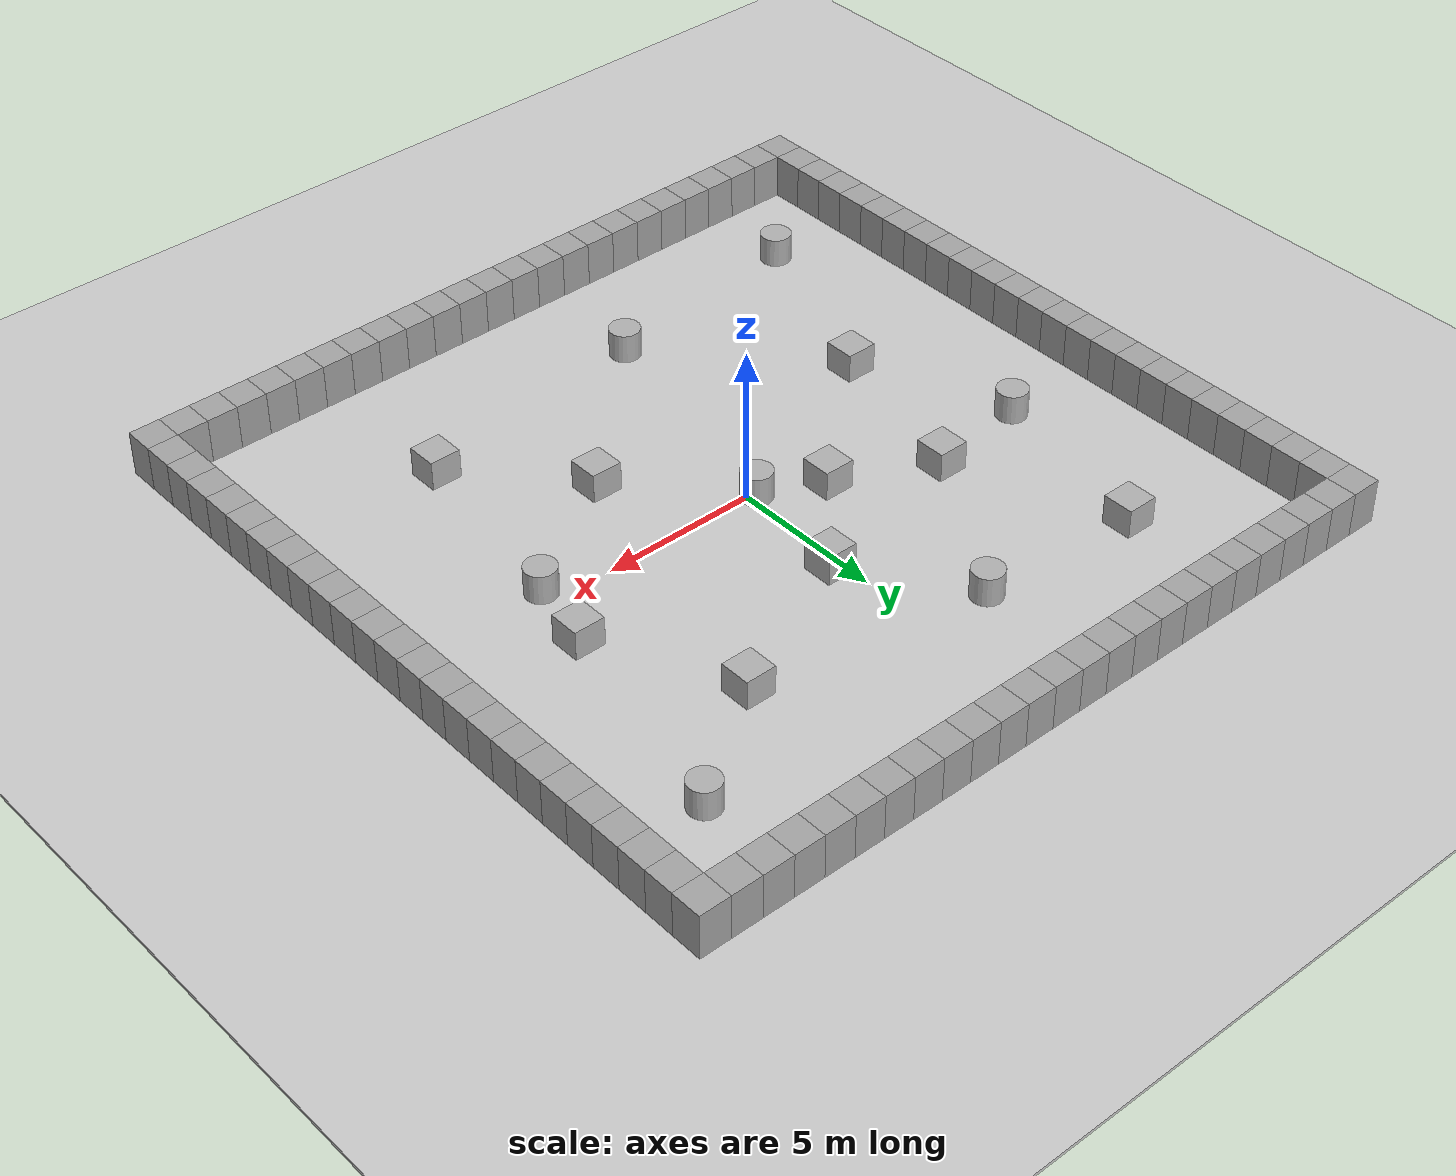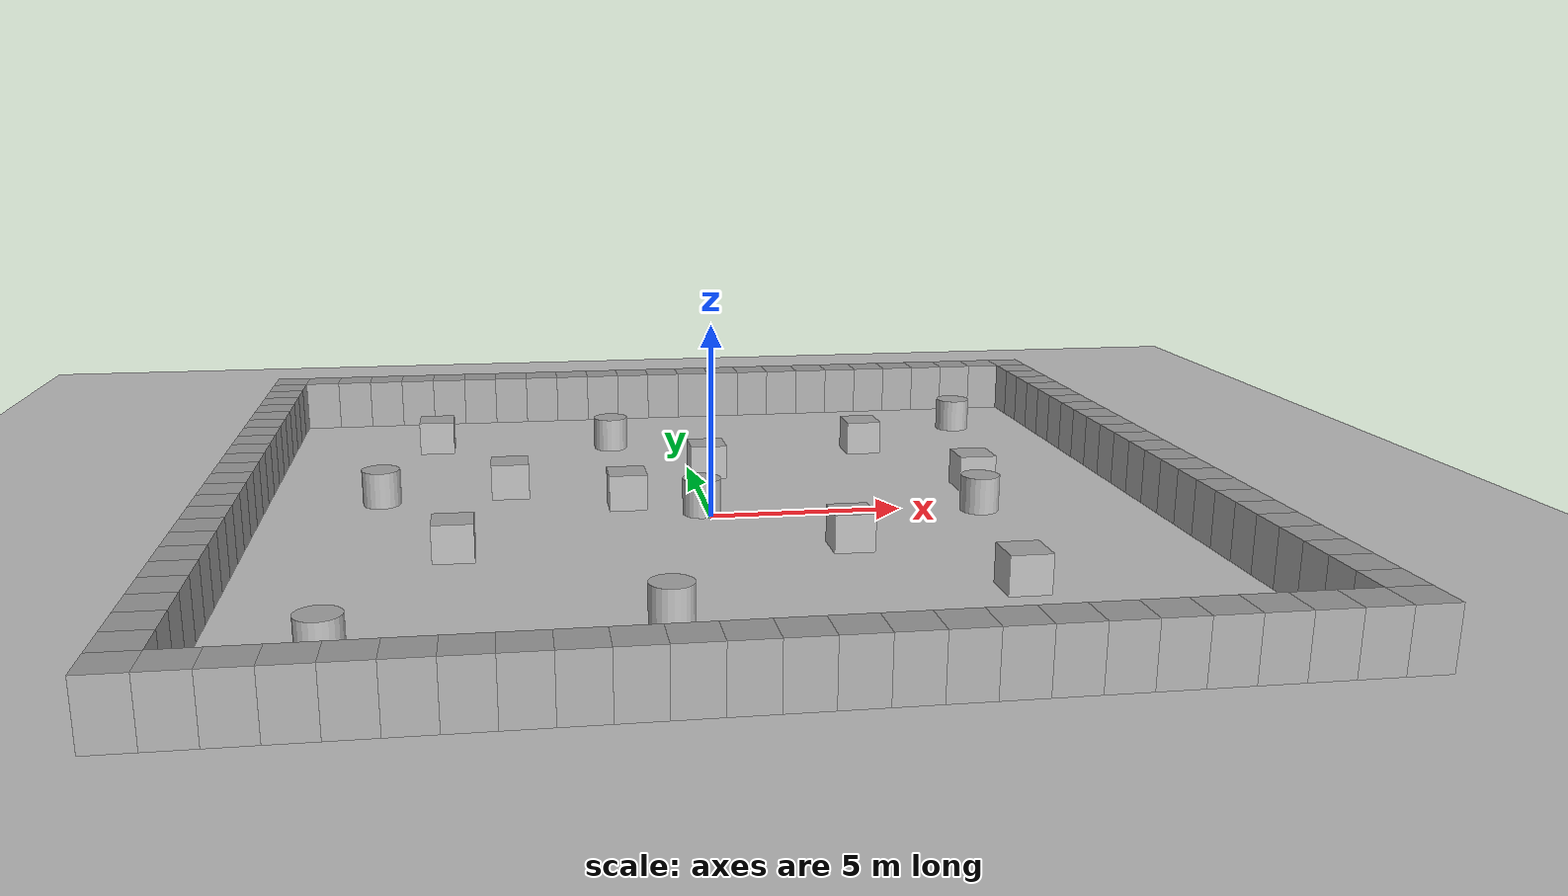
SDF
<sdf version='1.10'>
  <world name='empty'>
    <physics name='1ms' type='ignored'>
      <max_step_size>0.001</max_step_size>
      <real_time_factor>1</real_time_factor>
      <real_time_update_rate>1000</real_time_update_rate>
    </physics>
    <plugin name='gz::sim::systems::Physics' filename='gz-sim-physics-system'/>
    <plugin name='gz::sim::systems::UserCommands' filename='gz-sim-user-commands-system'/>
    <plugin name='gz::sim::systems::SceneBroadcaster' filename='gz-sim-scene-broadcaster-system'/>
    <plugin name='gz::sim::systems::Contact' filename='gz-sim-contact-system'/>
    <plugin filename="gz-sim-sensors-system" name="gz::sim::systems::Sensors">
      <render_engine>ogre2</render_engine>
    </plugin>
    <plugin filename="gz-sim-imu-system" name="gz::sim::systems::Imu"/>
    <gravity>0 0 -9.8000000000000007</gravity>
    <magnetic_field>5.5644999999999998e-06 2.2875799999999999e-05 -4.2388400000000002e-05</magnetic_field>
    <atmosphere type='adiabatic'/>
    <scene>
      <ambient>0.400000006 0.400000006 0.400000006 1</ambient>
      <background>0.699999988 0.699999988 0.699999988 1</background>
      <shadows>true</shadows>
    </scene>
    <model name='ground_plane'>
      <static>true</static>
      <link name='link'>
        <collision name='collision'>
          <geometry>
            <plane>
              <normal>0 0 1</normal>
              <size>100 100</size>
            </plane>
          </geometry>
          <surface>
            <friction>
              <ode/>
            </friction>
            <bounce/>
            <contact/>
          </surface>
        </collision>
        <visual name='visual'>
          <geometry>
            <plane>
              <normal>0 0 1</normal>
              <size>100 100</size>
            </plane>
          </geometry>
          <material>
            <ambient>0.800000012 0.800000012 0.800000012 1</ambient>
            <diffuse>0.800000012 0.800000012 0.800000012 1</diffuse>
            <specular>0.800000012 0.800000012 0.800000012 1</specular>
          </material>
        </visual>
        <pose>0 0 0 0 0 0</pose>
        <inertial>
          <pose>0 0 0 0 0 0</pose>
          <mass>1</mass>
          <inertia>
            <ixx>1</ixx>
            <ixy>0</ixy>
            <ixz>0</ixz>
            <iyy>1</iyy>
            <iyz>0</iyz>
            <izz>1</izz>
          </inertia>
        </inertial>
        <enable_wind>false</enable_wind>
      </link>
      <pose>0 0 0 0 0 0</pose>
      <self_collide>false</self_collide>
    </model>
    <model name='box'>
      <pose>-7.2664229478641413 8.001959563005741 0.5 0 0 0</pose>
      <link name='box_link'>
        <inertial>
          <inertia>
            <ixx>0.16666</ixx>
            <ixy>0</ixy>
            <ixz>0</ixz>
            <iyy>0.16666</iyy>
            <iyz>0</iyz>
            <izz>0.16666</izz>
          </inertia>
          <mass>1</mass>
          <pose>0 0 0 0 0 0</pose>
        </inertial>
        <collision name='box_collision'>
          <geometry>
            <box>
              <size>1 1 1</size>
            </box>
          </geometry>
          <surface>
            <friction>
              <ode/>
            </friction>
            <bounce/>
            <contact/>
          </surface>
        </collision>
        <visual name='box_visual'>
          <geometry>
            <box>
              <size>1 1 1</size>
            </box>
          </geometry>
          <material>
            <ambient>0.300000012 0.300000012 0.300000012 1</ambient>
            <diffuse>0.699999988 0.699999988 0.699999988 1</diffuse>
            <specular>1 1 1 1</specular>
          </material>
        </visual>
        <pose>0 0 0 0 0 0</pose>
        <enable_wind>false</enable_wind>
      </link>
      <static>false</static>
      <self_collide>false</self_collide>
    </model>
    <model name='box_0'>
      <pose>6.0330559122916796 -6.6597615887634198 0.5 0 0 0</pose>
      <link name='box_link'>
        <inertial>
          <inertia>
            <ixx>0.16666</ixx>
            <ixy>0</ixy>
            <ixz>0</ixz>
            <iyy>0.16666</iyy>
            <iyz>0</iyz>
            <izz>0.16666</izz>
          </inertia>
          <mass>1</mass>
          <pose>0 0 0 0 0 0</pose>
        </inertial>
        <collision name='box_collision'>
          <geometry>
            <box>
              <size>1 1 1</size>
            </box>
          </geometry>
          <surface>
            <friction>
              <ode/>
            </friction>
            <bounce/>
            <contact/>
          </surface>
        </collision>
        <visual name='box_visual'>
          <geometry>
            <box>
              <size>1 1 1</size>
            </box>
          </geometry>
          <material>
            <ambient>0.300000012 0.300000012 0.300000012 1</ambient>
            <diffuse>0.699999988 0.699999988 0.699999988 1</diffuse>
            <specular>1 1 1 1</specular>
          </material>
        </visual>
        <pose>0 0 0 0 0 0</pose>
        <enable_wind>false</enable_wind>
      </link>
      <static>false</static>
      <self_collide>false</self_collide>
    </model>
    <model name='box_1'>
      <pose>5.4431378589945663 6.2501473488965873 0.5 0 0 0</pose>
      <link name='box_link'>
        <inertial>
          <inertia>
            <ixx>0.16666</ixx>
            <ixy>0</ixy>
            <ixz>0</ixz>
            <iyy>0.16666</iyy>
            <iyz>0</iyz>
            <izz>0.16666</izz>
          </inertia>
          <mass>1</mass>
          <pose>0 0 0 0 0 0</pose>
        </inertial>
        <collision name='box_collision'>
          <geometry>
            <box>
              <size>1 1 1</size>
            </box>
          </geometry>
          <surface>
            <friction>
              <ode/>
            </friction>
            <bounce/>
            <contact/>
          </surface>
        </collision>
        <visual name='box_visual'>
          <geometry>
            <box>
              <size>1 1 1</size>
            </box>
          </geometry>
          <material>
            <ambient>0.300000012 0.300000012 0.300000012 1</ambient>
            <diffuse>0.699999988 0.699999988 0.699999988 1</diffuse>
            <specular>1 1 1 1</specular>
          </material>
        </visual>
        <pose>0 0 0 0 0 0</pose>
        <enable_wind>false</enable_wind>
      </link>
      <static>false</static>
      <self_collide>false</self_collide>
    </model>
    <model name='ground_plane_1'>
      <static>true</static>
      <link name='link'>
        <collision name='collision'>
          <geometry>
            <plane>
              <normal>0 0 1</normal>
              <size>100 100</size>
            </plane>
          </geometry>
          <surface>
            <friction>
              <ode/>
            </friction>
            <bounce/>
            <contact/>
          </surface>
        </collision>
        <visual name='visual'>
          <geometry>
            <plane>
              <normal>0 0 1</normal>
              <size>100 100</size>
            </plane>
          </geometry>
          <material>
            <ambient>0.800000012 0.800000012 0.800000012 1</ambient>
            <diffuse>0.800000012 0.800000012 0.800000012 1</diffuse>
            <specular>0.800000012 0.800000012 0.800000012 1</specular>
          </material>
        </visual>
      </link>
      <pose>5.8856477409981078 6.8674950587699826 0 0 0 0</pose>
      <self_collide>false</self_collide>
    </model>
    <model name='box_1_1'>
      <pose>-2.0925876761833555 1.1406302052938266 0.5 0 0 0</pose>
      <link name='box_link'>
        <inertial>
          <inertia>
            <ixx>0.16666</ixx>
            <ixy>0</ixy>
            <ixz>0</ixz>
            <iyy>0.16666</iyy>
            <iyz>0</iyz>
            <izz>0.16666</izz>
          </inertia>
          <mass>1</mass>
        </inertial>
        <collision name='box_collision'>
          <geometry>
            <box>
              <size>1 1 1</size>
            </box>
          </geometry>
          <surface>
            <friction>
              <ode/>
            </friction>
            <bounce/>
            <contact/>
          </surface>
        </collision>
        <visual name='box_visual'>
          <geometry>
            <box>
              <size>1 1 1</size>
            </box>
          </geometry>
          <material>
            <ambient>0.300000012 0.300000012 0.300000012 1</ambient>
            <diffuse>0.699999988 0.699999988 0.699999988 1</diffuse>
            <specular>1 1 1 1</specular>
          </material>
        </visual>
      </link>
      <static>false</static>
      <self_collide>false</self_collide>
    </model>
    <model name='box_1_2'>
      <pose>0.41984665652474096 3.952707647567669 0.5 0 0 0</pose>
      <link name='box_link'>
        <inertial>
          <inertia>
            <ixx>0.16666</ixx>
            <ixy>0</ixy>
            <ixz>0</ixz>
            <iyy>0.16666</iyy>
            <iyz>0</iyz>
            <izz>0.16666</izz>
          </inertia>
          <mass>1</mass>
        </inertial>
        <collision name='box_collision'>
          <geometry>
            <box>
              <size>1 1 1</size>
            </box>
          </geometry>
          <surface>
            <friction>
              <ode/>
            </friction>
            <bounce/>
            <contact/>
          </surface>
        </collision>
        <visual name='box_visual'>
          <geometry>
            <box>
              <size>1 1 1</size>
            </box>
          </geometry>
          <material>
            <ambient>0.300000012 0.300000012 0.300000012 1</ambient>
            <diffuse>0.699999988 0.699999988 0.699999988 1</diffuse>
            <specular>1 1 1 1</specular>
          </material>
        </visual>
      </link>
      <static>false</static>
      <self_collide>false</self_collide>
    </model>
    <model name='box_1_3'>
      <pose>2.9450058535421952 -3.1553020894889903 0.5 0 0 0</pose>
      <link name='box_link'>
        <inertial>
          <inertia>
            <ixx>0.16666</ixx>
            <ixy>0</ixy>
            <ixz>0</ixz>
            <iyy>0.16666</iyy>
            <iyz>0</iyz>
            <izz>0.16666</izz>
          </inertia>
          <mass>1</mass>
        </inertial>
        <collision name='box_collision'>
          <geometry>
            <box>
              <size>1 1 1</size>
            </box>
          </geometry>
          <surface>
            <friction>
              <ode/>
            </friction>
            <bounce/>
            <contact/>
          </surface>
        </collision>
        <visual name='box_visual'>
          <geometry>
            <box>
              <size>1 1 1</size>
            </box>
          </geometry>
          <material>
            <ambient>0.300000012 0.300000012 0.300000012 1</ambient>
            <diffuse>0.699999988 0.699999988 0.699999988 1</diffuse>
            <specular>1 1 1 1</specular>
          </material>
        </visual>
      </link>
      <static>false</static>
      <self_collide>false</self_collide>
    </model>
    <model name='box_1_4'>
      <pose>-6.5208503423678597 -2.643676608655257 0.5 0 0 0</pose>
      <link name='box_link'>
        <inertial>
          <inertia>
            <ixx>0.16666</ixx>
            <ixy>0</ixy>
            <ixz>0</ixz>
            <iyy>0.16666</iyy>
            <iyz>0</iyz>
            <izz>0.16666</izz>
          </inertia>
          <mass>1</mass>
        </inertial>
        <collision name='box_collision'>
          <geometry>
            <box>
              <size>1 1 1</size>
            </box>
          </geometry>
          <surface>
            <friction>
              <ode/>
            </friction>
            <bounce/>
            <contact/>
          </surface>
        </collision>
        <visual name='box_visual'>
          <geometry>
            <box>
              <size>1 1 1</size>
            </box>
          </geometry>
          <material>
            <ambient>0.300000012 0.300000012 0.300000012 1</ambient>
            <diffuse>0.699999988 0.699999988 0.699999988 1</diffuse>
            <specular>1 1 1 1</specular>
          </material>
        </visual>
      </link>
      <static>false</static>
      <self_collide>false</self_collide>
    </model>
    <model name='box_1_5'>
      <pose>-5.1389123843084468 2.6679012426387785 0.5 0 0 0</pose>
      <link name='box_link'>
        <inertial>
          <inertia>
            <ixx>0.16666</ixx>
            <ixy>0</ixy>
            <ixz>0</ixz>
            <iyy>0.16666</iyy>
            <iyz>0</iyz>
            <izz>0.16666</izz>
          </inertia>
          <mass>1</mass>
        </inertial>
        <collision name='box_collision'>
          <geometry>
            <box>
              <size>1 1 1</size>
            </box>
          </geometry>
          <surface>
            <friction>
              <ode/>
            </friction>
            <bounce/>
            <contact/>
          </surface>
        </collision>
        <visual name='box_visual'>
          <geometry>
            <box>
              <size>1 1 1</size>
            </box>
          </geometry>
          <material>
            <ambient>0.300000012 0.300000012 0.300000012 1</ambient>
            <diffuse>0.699999988 0.699999988 0.699999988 1</diffuse>
            <specular>1 1 1 1</specular>
          </material>
        </visual>
      </link>
      <static>false</static>
      <self_collide>false</self_collide>
    </model>
    <model name='box_1_6'>
      <pose>7.5589287411919539 1.7904647676761927 0.5 0 0 0</pose>
      <link name='box_link'>
        <inertial>
          <inertia>
            <ixx>0.16666</ixx>
            <ixy>0</ixy>
            <ixz>0</ixz>
            <iyy>0.16666</iyy>
            <iyz>0</iyz>
            <izz>0.16666</izz>
          </inertia>
          <mass>1</mass>
        </inertial>
        <collision name='box_collision'>
          <geometry>
            <box>
              <size>1 1 1</size>
            </box>
          </geometry>
          <surface>
            <friction>
              <ode/>
            </friction>
            <bounce/>
            <contact/>
          </surface>
        </collision>
        <visual name='box_visual'>
          <geometry>
            <box>
              <size>1 1 1</size>
            </box>
          </geometry>
          <material>
            <ambient>0.300000012 0.300000012 0.300000012 1</ambient>
            <diffuse>0.699999988 0.699999988 0.699999988 1</diffuse>
            <specular>1 1 1 1</specular>
          </material>
        </visual>
      </link>
      <static>false</static>
      <self_collide>false</self_collide>
    </model>
    <model name='cylinder'>
      <pose>-2.0379437450152151 7.5994624848365868 0.5 0 0 0</pose>
      <link name='cylinder_link'>
        <inertial>
          <inertia>
            <ixx>0.14580000000000001</ixx>
            <ixy>0</ixy>
            <ixz>0</ixz>
            <iyy>0.14580000000000001</iyy>
            <iyz>0</iyz>
            <izz>0.125</izz>
          </inertia>
          <mass>1</mass>
          <pose>0 0 0 0 0 0</pose>
        </inertial>
        <collision name='cylinder_collision'>
          <geometry>
            <cylinder>
              <radius>0.5</radius>
              <length>1</length>
            </cylinder>
          </geometry>
          <surface>
            <friction>
              <ode/>
            </friction>
            <bounce/>
            <contact/>
          </surface>
        </collision>
        <visual name='cylinder_visual'>
          <geometry>
            <cylinder>
              <radius>0.5</radius>
              <length>1</length>
            </cylinder>
          </geometry>
          <material>
            <ambient>0.300000012 0.300000012 0.300000012 1</ambient>
            <diffuse>0.699999988 0.699999988 0.699999988 1</diffuse>
            <specular>1 1 1 1</specular>
          </material>
        </visual>
        <pose>0 0 0 0 0 0</pose>
        <enable_wind>false</enable_wind>
      </link>
      <static>false</static>
      <self_collide>false</self_collide>
    </model>
    <model name='cylinder_1'>
      <pose>-8.5217671879853594 2.201041515387407 0.5 0 0 0</pose>
      <link name='cylinder_link'>
        <inertial>
          <inertia>
            <ixx>0.14580000000000001</ixx>
            <ixy>0</ixy>
            <ixz>0</ixz>
            <iyy>0.14580000000000001</iyy>
            <iyz>0</iyz>
            <izz>0.125</izz>
          </inertia>
          <mass>1</mass>
        </inertial>
        <collision name='cylinder_collision'>
          <geometry>
            <cylinder>
              <radius>0.5</radius>
              <length>1</length>
            </cylinder>
          </geometry>
          <surface>
            <friction>
              <ode/>
            </friction>
            <bounce/>
            <contact/>
          </surface>
        </collision>
        <visual name='cylinder_visual'>
          <geometry>
            <cylinder>
              <radius>0.5</radius>
              <length>1</length>
            </cylinder>
          </geometry>
          <material>
            <ambient>0.300000012 0.300000012 0.300000012 1</ambient>
            <diffuse>0.699999988 0.699999988 0.699999988 1</diffuse>
            <specular>1 1 1 1</specular>
          </material>
        </visual>
      </link>
      <static>false</static>
      <self_collide>false</self_collide>
    </model>
    <model name='cylinder_2'>
      <pose>-1.9285283423070976 -7.792672292694327 0.5 0 0 0</pose>
      <link name='cylinder_link'>
        <inertial>
          <inertia>
            <ixx>0.14580000000000001</ixx>
            <ixy>0</ixy>
            <ixz>0</ixz>
            <iyy>0.14580000000000001</iyy>
            <iyz>0</iyz>
            <izz>0.125</izz>
          </inertia>
          <mass>1</mass>
        </inertial>
        <collision name='cylinder_collision'>
          <geometry>
            <cylinder>
              <radius>0.5</radius>
              <length>1</length>
            </cylinder>
          </geometry>
          <surface>
            <friction>
              <ode/>
            </friction>
            <bounce/>
            <contact/>
          </surface>
        </collision>
        <visual name='cylinder_visual'>
          <geometry>
            <cylinder>
              <radius>0.5</radius>
              <length>1</length>
            </cylinder>
          </geometry>
          <material>
            <ambient>0.300000012 0.300000012 0.300000012 1</ambient>
            <diffuse>0.699999988 0.699999988 0.699999988 1</diffuse>
            <specular>1 1 1 1</specular>
          </material>
        </visual>
      </link>
      <static>false</static>
      <self_collide>false</self_collide>
    </model>
    <model name='cylinder_3'>
      <pose>-0.23170090689891465 0.17372997756641428 0.5 0 0 0</pose>
      <link name='cylinder_link'>
        <inertial>
          <inertia>
            <ixx>0.14580000000000001</ixx>
            <ixy>0</ixy>
            <ixz>0</ixz>
            <iyy>0.14580000000000001</iyy>
            <iyz>0</iyz>
            <izz>0.125</izz>
          </inertia>
          <mass>1</mass>
        </inertial>
        <collision name='cylinder_collision'>
          <geometry>
            <cylinder>
              <radius>0.5</radius>
              <length>1</length>
            </cylinder>
          </geometry>
          <surface>
            <friction>
              <ode/>
            </friction>
            <bounce/>
            <contact/>
          </surface>
        </collision>
        <visual name='cylinder_visual'>
          <geometry>
            <cylinder>
              <radius>0.5</radius>
              <length>1</length>
            </cylinder>
          </geometry>
          <material>
            <ambient>0.300000012 0.300000012 0.300000012 1</ambient>
            <diffuse>0.699999988 0.699999988 0.699999988 1</diffuse>
            <specular>1 1 1 1</specular>
          </material>
        </visual>
      </link>
      <static>false</static>
      <self_collide>false</self_collide>
    </model>
    <model name='cylinder_4'>
      <pose>9.0908475155126158 8.7140515046431091 0.5 0 0 0</pose>
      <link name='cylinder_link'>
        <inertial>
          <inertia>
            <ixx>0.14580000000000001</ixx>
            <ixy>0</ixy>
            <ixz>0</ixz>
            <iyy>0.14580000000000001</iyy>
            <iyz>0</iyz>
            <izz>0.125</izz>
          </inertia>
          <mass>1</mass>
        </inertial>
        <collision name='cylinder_collision'>
          <geometry>
            <cylinder>
              <radius>0.5</radius>
              <length>1</length>
            </cylinder>
          </geometry>
          <surface>
            <friction>
              <ode/>
            </friction>
            <bounce/>
            <contact/>
          </surface>
        </collision>
        <visual name='cylinder_visual'>
          <geometry>
            <cylinder>
              <radius>0.5</radius>
              <length>1</length>
            </cylinder>
          </geometry>
          <material>
            <ambient>0.300000012 0.300000012 0.300000012 1</ambient>
            <diffuse>0.699999988 0.699999988 0.699999988 1</diffuse>
            <specular>1 1 1 1</specular>
          </material>
        </visual>
      </link>
      <static>false</static>
      <self_collide>false</self_collide>
    </model>
    <model name='cylinder_5'>
      <pose>-8.9233435822444385 -8.7101261716177483 0.5 0 0 0</pose>
      <link name='cylinder_link'>
        <inertial>
          <inertia>
            <ixx>0.14580000000000001</ixx>
            <ixy>0</ixy>
            <ixz>0</ixz>
            <iyy>0.14580000000000001</iyy>
            <iyz>0</iyz>
            <izz>0.125</izz>
          </inertia>
          <mass>1</mass>
        </inertial>
        <collision name='cylinder_collision'>
          <geometry>
            <cylinder>
              <radius>0.5</radius>
              <length>1</length>
            </cylinder>
          </geometry>
          <surface>
            <friction>
              <ode/>
            </friction>
            <bounce/>
            <contact/>
          </surface>
        </collision>
        <visual name='cylinder_visual'>
          <geometry>
            <cylinder>
              <radius>0.5</radius>
              <length>1</length>
            </cylinder>
          </geometry>
          <material>
            <ambient>0.300000012 0.300000012 0.300000012 1</ambient>
            <diffuse>0.699999988 0.699999988 0.699999988 1</diffuse>
            <specular>1 1 1 1</specular>
          </material>
        </visual>
      </link>
      <static>false</static>
      <self_collide>false</self_collide>
    </model>
    <model name='cylinder_6'>
      <pose>7.0176003287278821 -0.52406950820931186 0.5 0 0 0</pose>
      <link name='cylinder_link'>
        <inertial>
          <inertia>
            <ixx>0.14580000000000001</ixx>
            <ixy>0</ixy>
            <ixz>0</ixz>
            <iyy>0.14580000000000001</iyy>
            <iyz>0</iyz>
            <izz>0.125</izz>
          </inertia>
          <mass>1</mass>
        </inertial>
        <collision name='cylinder_collision'>
          <geometry>
            <cylinder>
              <radius>0.5</radius>
              <length>1</length>
            </cylinder>
          </geometry>
          <surface>
            <friction>
              <ode/>
            </friction>
            <bounce/>
            <contact/>
          </surface>
        </collision>
        <visual name='cylinder_visual'>
          <geometry>
            <cylinder>
              <radius>0.5</radius>
              <length>1</length>
            </cylinder>
          </geometry>
          <material>
            <ambient>0.300000012 0.300000012 0.300000012 1</ambient>
            <diffuse>0.699999988 0.699999988 0.699999988 1</diffuse>
            <specular>1 1 1 1</specular>
          </material>
        </visual>
      </link>
      <static>false</static>
      <self_collide>false</self_collide>
    </model>
    <model name='wall_box_0'>
      <static>true</static>
      <pose>-12.0 -12.0 0.75 0 0 0</pose>
      <link name='link'>
        <collision name='collision'>
          <geometry>
            <box>
              <size>1.0 1.0 1.5</size>
            </box>
          </geometry>
          <surface>
            <friction>
              <ode/>
            </friction>
            <bounce/>
            <contact/>
          </surface>
        </collision>
        <visual name='visual'>
          <geometry>
            <box>
              <size>1.0 1.0 1.5</size>
            </box>
          </geometry>
          <material>
            <ambient>0.55 0.55 0.55 1</ambient>
            <diffuse>0.65 0.65 0.65 1</diffuse>
            <specular>0.3 0.3 0.3 1</specular>
          </material>
        </visual>
      </link>
    </model>

    <model name='wall_box_1'>
      <static>true</static>
      <pose>-12.0 -11.0 0.75 0 0 0</pose>
      <link name='link'>
        <collision name='collision'>
          <geometry>
            <box>
              <size>1.0 1.0 1.5</size>
            </box>
          </geometry>
          <surface>
            <friction>
              <ode/>
            </friction>
            <bounce/>
            <contact/>
          </surface>
        </collision>
        <visual name='visual'>
          <geometry>
            <box>
              <size>1.0 1.0 1.5</size>
            </box>
          </geometry>
          <material>
            <ambient>0.55 0.55 0.55 1</ambient>
            <diffuse>0.65 0.65 0.65 1</diffuse>
            <specular>0.3 0.3 0.3 1</specular>
          </material>
        </visual>
      </link>
    </model>

    <model name='wall_box_2'>
      <static>true</static>
      <pose>-12.0 -10.0 0.75 0 0 0</pose>
      <link name='link'>
        <collision name='collision'>
          <geometry>
            <box>
              <size>1.0 1.0 1.5</size>
            </box>
          </geometry>
          <surface>
            <friction>
              <ode/>
            </friction>
            <bounce/>
            <contact/>
          </surface>
        </collision>
        <visual name='visual'>
          <geometry>
            <box>
              <size>1.0 1.0 1.5</size>
            </box>
          </geometry>
          <material>
            <ambient>0.55 0.55 0.55 1</ambient>
            <diffuse>0.65 0.65 0.65 1</diffuse>
            <specular>0.3 0.3 0.3 1</specular>
          </material>
        </visual>
      </link>
    </model>

    <model name='wall_box_3'>
      <static>true</static>
      <pose>-12.0 -9.0 0.75 0 0 0</pose>
      <link name='link'>
        <collision name='collision'>
          <geometry>
            <box>
              <size>1.0 1.0 1.5</size>
            </box>
          </geometry>
          <surface>
            <friction>
              <ode/>
            </friction>
            <bounce/>
            <contact/>
          </surface>
        </collision>
        <visual name='visual'>
          <geometry>
            <box>
              <size>1.0 1.0 1.5</size>
            </box>
          </geometry>
          <material>
            <ambient>0.55 0.55 0.55 1</ambient>
            <diffuse>0.65 0.65 0.65 1</diffuse>
            <specular>0.3 0.3 0.3 1</specular>
          </material>
        </visual>
      </link>
    </model>

    <model name='wall_box_4'>
      <static>true</static>
      <pose>-12.0 -8.0 0.75 0 0 0</pose>
      <link name='link'>
        <collision name='collision'>
          <geometry>
            <box>
              <size>1.0 1.0 1.5</size>
            </box>
          </geometry>
          <surface>
            <friction>
              <ode/>
            </friction>
            <bounce/>
            <contact/>
          </surface>
        </collision>
        <visual name='visual'>
          <geometry>
            <box>
              <size>1.0 1.0 1.5</size>
            </box>
          </geometry>
          <material>
            <ambient>0.55 0.55 0.55 1</ambient>
            <diffuse>0.65 0.65 0.65 1</diffuse>
            <specular>0.3 0.3 0.3 1</specular>
          </material>
        </visual>
      </link>
    </model>

    <model name='wall_box_5'>
      <static>true</static>
      <pose>-12.0 -7.0 0.75 0 0 0</pose>
      <link name='link'>
        <collision name='collision'>
          <geometry>
            <box>
              <size>1.0 1.0 1.5</size>
            </box>
          </geometry>
          <surface>
            <friction>
              <ode/>
            </friction>
            <bounce/>
            <contact/>
          </surface>
        </collision>
        <visual name='visual'>
          <geometry>
            <box>
              <size>1.0 1.0 1.5</size>
            </box>
          </geometry>
          <material>
            <ambient>0.55 0.55 0.55 1</ambient>
            <diffuse>0.65 0.65 0.65 1</diffuse>
            <specular>0.3 0.3 0.3 1</specular>
          </material>
        </visual>
      </link>
    </model>

    <model name='wall_box_6'>
      <static>true</static>
      <pose>-12.0 -6.0 0.75 0 0 0</pose>
      <link name='link'>
        <collision name='collision'>
          <geometry>
            <box>
              <size>1.0 1.0 1.5</size>
            </box>
          </geometry>
          <surface>
            <friction>
              <ode/>
            </friction>
            <bounce/>
            <contact/>
          </surface>
        </collision>
        <visual name='visual'>
          <geometry>
            <box>
              <size>1.0 1.0 1.5</size>
            </box>
          </geometry>
          <material>
            <ambient>0.55 0.55 0.55 1</ambient>
            <diffuse>0.65 0.65 0.65 1</diffuse>
            <specular>0.3 0.3 0.3 1</specular>
          </material>
        </visual>
      </link>
    </model>

    <model name='wall_box_7'>
      <static>true</static>
      <pose>-12.0 -5.0 0.75 0 0 0</pose>
      <link name='link'>
        <collision name='collision'>
          <geometry>
            <box>
              <size>1.0 1.0 1.5</size>
            </box>
          </geometry>
          <surface>
            <friction>
              <ode/>
            </friction>
            <bounce/>
            <contact/>
          </surface>
        </collision>
        <visual name='visual'>
          <geometry>
            <box>
              <size>1.0 1.0 1.5</size>
            </box>
          </geometry>
          <material>
            <ambient>0.55 0.55 0.55 1</ambient>
            <diffuse>0.65 0.65 0.65 1</diffuse>
            <specular>0.3 0.3 0.3 1</specular>
          </material>
        </visual>
      </link>
    </model>

    <model name='wall_box_8'>
      <static>true</static>
      <pose>-12.0 -4.0 0.75 0 0 0</pose>
      <link name='link'>
        <collision name='collision'>
          <geometry>
            <box>
              <size>1.0 1.0 1.5</size>
            </box>
          </geometry>
          <surface>
            <friction>
              <ode/>
            </friction>
            <bounce/>
            <contact/>
          </surface>
        </collision>
        <visual name='visual'>
          <geometry>
            <box>
              <size>1.0 1.0 1.5</size>
            </box>
          </geometry>
          <material>
            <ambient>0.55 0.55 0.55 1</ambient>
            <diffuse>0.65 0.65 0.65 1</diffuse>
            <specular>0.3 0.3 0.3 1</specular>
          </material>
        </visual>
      </link>
    </model>

    <model name='wall_box_9'>
      <static>true</static>
      <pose>-12.0 -3.0 0.75 0 0 0</pose>
      <link name='link'>
        <collision name='collision'>
          <geometry>
            <box>
              <size>1.0 1.0 1.5</size>
            </box>
          </geometry>
          <surface>
            <friction>
              <ode/>
            </friction>
            <bounce/>
            <contact/>
          </surface>
        </collision>
        <visual name='visual'>
          <geometry>
            <box>
              <size>1.0 1.0 1.5</size>
            </box>
          </geometry>
          <material>
            <ambient>0.55 0.55 0.55 1</ambient>
            <diffuse>0.65 0.65 0.65 1</diffuse>
            <specular>0.3 0.3 0.3 1</specular>
          </material>
        </visual>
      </link>
    </model>

    <model name='wall_box_10'>
      <static>true</static>
      <pose>-12.0 -2.0 0.75 0 0 0</pose>
      <link name='link'>
        <collision name='collision'>
          <geometry>
            <box>
              <size>1.0 1.0 1.5</size>
            </box>
          </geometry>
          <surface>
            <friction>
              <ode/>
            </friction>
            <bounce/>
            <contact/>
          </surface>
        </collision>
        <visual name='visual'>
          <geometry>
            <box>
              <size>1.0 1.0 1.5</size>
            </box>
          </geometry>
          <material>
            <ambient>0.55 0.55 0.55 1</ambient>
            <diffuse>0.65 0.65 0.65 1</diffuse>
            <specular>0.3 0.3 0.3 1</specular>
          </material>
        </visual>
      </link>
    </model>

    <model name='wall_box_11'>
      <static>true</static>
      <pose>-12.0 -1.0 0.75 0 0 0</pose>
      <link name='link'>
        <collision name='collision'>
          <geometry>
            <box>
              <size>1.0 1.0 1.5</size>
            </box>
          </geometry>
          <surface>
            <friction>
              <ode/>
            </friction>
            <bounce/>
            <contact/>
          </surface>
        </collision>
        <visual name='visual'>
          <geometry>
            <box>
              <size>1.0 1.0 1.5</size>
            </box>
          </geometry>
          <material>
            <ambient>0.55 0.55 0.55 1</ambient>
            <diffuse>0.65 0.65 0.65 1</diffuse>
            <specular>0.3 0.3 0.3 1</specular>
          </material>
        </visual>
      </link>
    </model>

    <model name='wall_box_12'>
      <static>true</static>
      <pose>-12.0 0.0 0.75 0 0 0</pose>
      <link name='link'>
        <collision name='collision'>
          <geometry>
            <box>
              <size>1.0 1.0 1.5</size>
            </box>
          </geometry>
          <surface>
            <friction>
              <ode/>
            </friction>
            <bounce/>
            <contact/>
          </surface>
        </collision>
        <visual name='visual'>
          <geometry>
            <box>
              <size>1.0 1.0 1.5</size>
            </box>
          </geometry>
          <material>
            <ambient>0.55 0.55 0.55 1</ambient>
            <diffuse>0.65 0.65 0.65 1</diffuse>
            <specular>0.3 0.3 0.3 1</specular>
          </material>
        </visual>
      </link>
    </model>

    <model name='wall_box_13'>
      <static>true</static>
      <pose>-12.0 1.0 0.75 0 0 0</pose>
      <link name='link'>
        <collision name='collision'>
          <geometry>
            <box>
              <size>1.0 1.0 1.5</size>
            </box>
          </geometry>
          <surface>
            <friction>
              <ode/>
            </friction>
            <bounce/>
            <contact/>
          </surface>
        </collision>
        <visual name='visual'>
          <geometry>
            <box>
              <size>1.0 1.0 1.5</size>
            </box>
          </geometry>
          <material>
            <ambient>0.55 0.55 0.55 1</ambient>
            <diffuse>0.65 0.65 0.65 1</diffuse>
            <specular>0.3 0.3 0.3 1</specular>
          </material>
        </visual>
      </link>
    </model>

    <model name='wall_box_14'>
      <static>true</static>
      <pose>-12.0 2.0 0.75 0 0 0</pose>
      <link name='link'>
        <collision name='collision'>
          <geometry>
            <box>
              <size>1.0 1.0 1.5</size>
            </box>
          </geometry>
          <surface>
            <friction>
              <ode/>
            </friction>
            <bounce/>
            <contact/>
          </surface>
        </collision>
        <visual name='visual'>
          <geometry>
            <box>
              <size>1.0 1.0 1.5</size>
            </box>
          </geometry>
          <material>
            <ambient>0.55 0.55 0.55 1</ambient>
            <diffuse>0.65 0.65 0.65 1</diffuse>
            <specular>0.3 0.3 0.3 1</specular>
          </material>
        </visual>
      </link>
    </model>

    <model name='wall_box_15'>
      <static>true</static>
      <pose>-12.0 3.0 0.75 0 0 0</pose>
      <link name='link'>
        <collision name='collision'>
          <geometry>
            <box>
              <size>1.0 1.0 1.5</size>
            </box>
          </geometry>
          <surface>
            <friction>
              <ode/>
            </friction>
            <bounce/>
            <contact/>
          </surface>
        </collision>
        <visual name='visual'>
          <geometry>
            <box>
              <size>1.0 1.0 1.5</size>
            </box>
          </geometry>
          <material>
            <ambient>0.55 0.55 0.55 1</ambient>
            <diffuse>0.65 0.65 0.65 1</diffuse>
            <specular>0.3 0.3 0.3 1</specular>
          </material>
        </visual>
      </link>
    </model>

    <model name='wall_box_16'>
      <static>true</static>
      <pose>-12.0 4.0 0.75 0 0 0</pose>
      <link name='link'>
        <collision name='collision'>
          <geometry>
            <box>
              <size>1.0 1.0 1.5</size>
            </box>
          </geometry>
          <surface>
            <friction>
              <ode/>
            </friction>
            <bounce/>
            <contact/>
          </surface>
        </collision>
        <visual name='visual'>
          <geometry>
            <box>
              <size>1.0 1.0 1.5</size>
            </box>
          </geometry>
          <material>
            <ambient>0.55 0.55 0.55 1</ambient>
            <diffuse>0.65 0.65 0.65 1</diffuse>
            <specular>0.3 0.3 0.3 1</specular>
          </material>
        </visual>
      </link>
    </model>

    <model name='wall_box_17'>
      <static>true</static>
      <pose>-12.0 5.0 0.75 0 0 0</pose>
      <link name='link'>
        <collision name='collision'>
          <geometry>
            <box>
              <size>1.0 1.0 1.5</size>
            </box>
          </geometry>
          <surface>
            <friction>
              <ode/>
            </friction>
            <bounce/>
            <contact/>
          </surface>
        </collision>
        <visual name='visual'>
          <geometry>
            <box>
              <size>1.0 1.0 1.5</size>
            </box>
          </geometry>
          <material>
            <ambient>0.55 0.55 0.55 1</ambient>
            <diffuse>0.65 0.65 0.65 1</diffuse>
            <specular>0.3 0.3 0.3 1</specular>
          </material>
        </visual>
      </link>
    </model>

    <model name='wall_box_18'>
      <static>true</static>
      <pose>-12.0 6.0 0.75 0 0 0</pose>
      <link name='link'>
        <collision name='collision'>
          <geometry>
            <box>
              <size>1.0 1.0 1.5</size>
            </box>
          </geometry>
          <surface>
            <friction>
              <ode/>
            </friction>
            <bounce/>
            <contact/>
          </surface>
        </collision>
        <visual name='visual'>
          <geometry>
            <box>
              <size>1.0 1.0 1.5</size>
            </box>
          </geometry>
          <material>
            <ambient>0.55 0.55 0.55 1</ambient>
            <diffuse>0.65 0.65 0.65 1</diffuse>
            <specular>0.3 0.3 0.3 1</specular>
          </material>
        </visual>
      </link>
    </model>

    <model name='wall_box_19'>
      <static>true</static>
      <pose>-12.0 7.0 0.75 0 0 0</pose>
      <link name='link'>
        <collision name='collision'>
          <geometry>
            <box>
              <size>1.0 1.0 1.5</size>
            </box>
          </geometry>
          <surface>
            <friction>
              <ode/>
            </friction>
            <bounce/>
            <contact/>
          </surface>
        </collision>
        <visual name='visual'>
          <geometry>
            <box>
              <size>1.0 1.0 1.5</size>
            </box>
          </geometry>
          <material>
            <ambient>0.55 0.55 0.55 1</ambient>
            <diffuse>0.65 0.65 0.65 1</diffuse>
            <specular>0.3 0.3 0.3 1</specular>
          </material>
        </visual>
      </link>
    </model>

    <model name='wall_box_20'>
      <static>true</static>
      <pose>-12.0 8.0 0.75 0 0 0</pose>
      <link name='link'>
        <collision name='collision'>
          <geometry>
            <box>
              <size>1.0 1.0 1.5</size>
            </box>
          </geometry>
          <surface>
            <friction>
              <ode/>
            </friction>
            <bounce/>
            <contact/>
          </surface>
        </collision>
        <visual name='visual'>
          <geometry>
            <box>
              <size>1.0 1.0 1.5</size>
            </box>
          </geometry>
          <material>
            <ambient>0.55 0.55 0.55 1</ambient>
            <diffuse>0.65 0.65 0.65 1</diffuse>
            <specular>0.3 0.3 0.3 1</specular>
          </material>
        </visual>
      </link>
    </model>

    <model name='wall_box_21'>
      <static>true</static>
      <pose>-12.0 9.0 0.75 0 0 0</pose>
      <link name='link'>
        <collision name='collision'>
          <geometry>
            <box>
              <size>1.0 1.0 1.5</size>
            </box>
          </geometry>
          <surface>
            <friction>
              <ode/>
            </friction>
            <bounce/>
            <contact/>
          </surface>
        </collision>
        <visual name='visual'>
          <geometry>
            <box>
              <size>1.0 1.0 1.5</size>
            </box>
          </geometry>
          <material>
            <ambient>0.55 0.55 0.55 1</ambient>
            <diffuse>0.65 0.65 0.65 1</diffuse>
            <specular>0.3 0.3 0.3 1</specular>
          </material>
        </visual>
      </link>
    </model>

    <model name='wall_box_22'>
      <static>true</static>
      <pose>-12.0 10.0 0.75 0 0 0</pose>
      <link name='link'>
        <collision name='collision'>
          <geometry>
            <box>
              <size>1.0 1.0 1.5</size>
            </box>
          </geometry>
          <surface>
            <friction>
              <ode/>
            </friction>
            <bounce/>
            <contact/>
          </surface>
        </collision>
        <visual name='visual'>
          <geometry>
            <box>
              <size>1.0 1.0 1.5</size>
            </box>
          </geometry>
          <material>
            <ambient>0.55 0.55 0.55 1</ambient>
            <diffuse>0.65 0.65 0.65 1</diffuse>
            <specular>0.3 0.3 0.3 1</specular>
          </material>
        </visual>
      </link>
    </model>

    <model name='wall_box_23'>
      <static>true</static>
      <pose>-12.0 11.0 0.75 0 0 0</pose>
      <link name='link'>
        <collision name='collision'>
          <geometry>
            <box>
              <size>1.0 1.0 1.5</size>
            </box>
          </geometry>
          <surface>
            <friction>
              <ode/>
            </friction>
            <bounce/>
            <contact/>
          </surface>
        </collision>
        <visual name='visual'>
          <geometry>
            <box>
              <size>1.0 1.0 1.5</size>
            </box>
          </geometry>
          <material>
            <ambient>0.55 0.55 0.55 1</ambient>
            <diffuse>0.65 0.65 0.65 1</diffuse>
            <specular>0.3 0.3 0.3 1</specular>
          </material>
        </visual>
      </link>
    </model>

    <model name='wall_box_24'>
      <static>true</static>
      <pose>-12.0 12.0 0.75 0 0 0</pose>
      <link name='link'>
        <collision name='collision'>
          <geometry>
            <box>
              <size>1.0 1.0 1.5</size>
            </box>
          </geometry>
          <surface>
            <friction>
              <ode/>
            </friction>
            <bounce/>
            <contact/>
          </surface>
        </collision>
        <visual name='visual'>
          <geometry>
            <box>
              <size>1.0 1.0 1.5</size>
            </box>
          </geometry>
          <material>
            <ambient>0.55 0.55 0.55 1</ambient>
            <diffuse>0.65 0.65 0.65 1</diffuse>
            <specular>0.3 0.3 0.3 1</specular>
          </material>
        </visual>
      </link>
    </model>

    <model name='wall_box_25'>
      <static>true</static>
      <pose>-11.0 -12.0 0.75 0 0 0</pose>
      <link name='link'>
        <collision name='collision'>
          <geometry>
            <box>
              <size>1.0 1.0 1.5</size>
            </box>
          </geometry>
          <surface>
            <friction>
              <ode/>
            </friction>
            <bounce/>
            <contact/>
          </surface>
        </collision>
        <visual name='visual'>
          <geometry>
            <box>
              <size>1.0 1.0 1.5</size>
            </box>
          </geometry>
          <material>
            <ambient>0.55 0.55 0.55 1</ambient>
            <diffuse>0.65 0.65 0.65 1</diffuse>
            <specular>0.3 0.3 0.3 1</specular>
          </material>
        </visual>
      </link>
    </model>

    <model name='wall_box_26'>
      <static>true</static>
      <pose>-11.0 12.0 0.75 0 0 0</pose>
      <link name='link'>
        <collision name='collision'>
          <geometry>
            <box>
              <size>1.0 1.0 1.5</size>
            </box>
          </geometry>
          <surface>
            <friction>
              <ode/>
            </friction>
            <bounce/>
            <contact/>
          </surface>
        </collision>
        <visual name='visual'>
          <geometry>
            <box>
              <size>1.0 1.0 1.5</size>
            </box>
          </geometry>
          <material>
            <ambient>0.55 0.55 0.55 1</ambient>
            <diffuse>0.65 0.65 0.65 1</diffuse>
            <specular>0.3 0.3 0.3 1</specular>
          </material>
        </visual>
      </link>
    </model>

    <model name='wall_box_27'>
      <static>true</static>
      <pose>-10.0 -12.0 0.75 0 0 0</pose>
      <link name='link'>
        <collision name='collision'>
          <geometry>
            <box>
              <size>1.0 1.0 1.5</size>
            </box>
          </geometry>
          <surface>
            <friction>
              <ode/>
            </friction>
            <bounce/>
            <contact/>
          </surface>
        </collision>
        <visual name='visual'>
          <geometry>
            <box>
              <size>1.0 1.0 1.5</size>
            </box>
          </geometry>
          <material>
            <ambient>0.55 0.55 0.55 1</ambient>
            <diffuse>0.65 0.65 0.65 1</diffuse>
            <specular>0.3 0.3 0.3 1</specular>
          </material>
        </visual>
      </link>
    </model>

    <model name='wall_box_28'>
      <static>true</static>
      <pose>-10.0 12.0 0.75 0 0 0</pose>
      <link name='link'>
        <collision name='collision'>
          <geometry>
            <box>
              <size>1.0 1.0 1.5</size>
            </box>
          </geometry>
          <surface>
            <friction>
              <ode/>
            </friction>
            <bounce/>
            <contact/>
          </surface>
        </collision>
        <visual name='visual'>
          <geometry>
            <box>
              <size>1.0 1.0 1.5</size>
            </box>
          </geometry>
          <material>
            <ambient>0.55 0.55 0.55 1</ambient>
            <diffuse>0.65 0.65 0.65 1</diffuse>
            <specular>0.3 0.3 0.3 1</specular>
          </material>
        </visual>
      </link>
    </model>

    <model name='wall_box_29'>
      <static>true</static>
      <pose>-9.0 -12.0 0.75 0 0 0</pose>
      <link name='link'>
        <collision name='collision'>
          <geometry>
            <box>
              <size>1.0 1.0 1.5</size>
            </box>
          </geometry>
          <surface>
            <friction>
              <ode/>
            </friction>
            <bounce/>
            <contact/>
          </surface>
        </collision>
        <visual name='visual'>
          <geometry>
            <box>
              <size>1.0 1.0 1.5</size>
            </box>
          </geometry>
          <material>
            <ambient>0.55 0.55 0.55 1</ambient>
            <diffuse>0.65 0.65 0.65 1</diffuse>
            <specular>0.3 0.3 0.3 1</specular>
          </material>
        </visual>
      </link>
    </model>

    <model name='wall_box_30'>
      <static>true</static>
      <pose>-9.0 12.0 0.75 0 0 0</pose>
      <link name='link'>
        <collision name='collision'>
          <geometry>
            <box>
              <size>1.0 1.0 1.5</size>
            </box>
          </geometry>
          <surface>
            <friction>
              <ode/>
            </friction>
            <bounce/>
            <contact/>
          </surface>
        </collision>
        <visual name='visual'>
          <geometry>
            <box>
              <size>1.0 1.0 1.5</size>
            </box>
          </geometry>
          <material>
            <ambient>0.55 0.55 0.55 1</ambient>
            <diffuse>0.65 0.65 0.65 1</diffuse>
            <specular>0.3 0.3 0.3 1</specular>
          </material>
        </visual>
      </link>
    </model>

    <model name='wall_box_31'>
      <static>true</static>
      <pose>-8.0 -12.0 0.75 0 0 0</pose>
      <link name='link'>
        <collision name='collision'>
          <geometry>
            <box>
              <size>1.0 1.0 1.5</size>
            </box>
          </geometry>
          <surface>
            <friction>
              <ode/>
            </friction>
            <bounce/>
            <contact/>
          </surface>
        </collision>
        <visual name='visual'>
          <geometry>
            <box>
              <size>1.0 1.0 1.5</size>
            </box>
          </geometry>
          <material>
            <ambient>0.55 0.55 0.55 1</ambient>
            <diffuse>0.65 0.65 0.65 1</diffuse>
            <specular>0.3 0.3 0.3 1</specular>
          </material>
        </visual>
      </link>
    </model>

    <model name='wall_box_32'>
      <static>true</static>
      <pose>-8.0 12.0 0.75 0 0 0</pose>
      <link name='link'>
        <collision name='collision'>
          <geometry>
            <box>
              <size>1.0 1.0 1.5</size>
            </box>
          </geometry>
          <surface>
            <friction>
              <ode/>
            </friction>
            <bounce/>
            <contact/>
          </surface>
        </collision>
        <visual name='visual'>
          <geometry>
            <box>
              <size>1.0 1.0 1.5</size>
            </box>
          </geometry>
          <material>
            <ambient>0.55 0.55 0.55 1</ambient>
            <diffuse>0.65 0.65 0.65 1</diffuse>
            <specular>0.3 0.3 0.3 1</specular>
          </material>
        </visual>
      </link>
    </model>

    <model name='wall_box_33'>
      <static>true</static>
      <pose>-7.0 -12.0 0.75 0 0 0</pose>
      <link name='link'>
        <collision name='collision'>
          <geometry>
            <box>
              <size>1.0 1.0 1.5</size>
            </box>
          </geometry>
          <surface>
            <friction>
              <ode/>
            </friction>
            <bounce/>
            <contact/>
          </surface>
        </collision>
        <visual name='visual'>
          <geometry>
            <box>
              <size>1.0 1.0 1.5</size>
            </box>
          </geometry>
          <material>
            <ambient>0.55 0.55 0.55 1</ambient>
            <diffuse>0.65 0.65 0.65 1</diffuse>
            <specular>0.3 0.3 0.3 1</specular>
          </material>
        </visual>
      </link>
    </model>

    <model name='wall_box_34'>
      <static>true</static>
      <pose>-7.0 12.0 0.75 0 0 0</pose>
      <link name='link'>
        <collision name='collision'>
          <geometry>
            <box>
              <size>1.0 1.0 1.5</size>
            </box>
          </geometry>
          <surface>
            <friction>
              <ode/>
            </friction>
            <bounce/>
            <contact/>
          </surface>
        </collision>
        <visual name='visual'>
          <geometry>
            <box>
              <size>1.0 1.0 1.5</size>
            </box>
          </geometry>
          <material>
            <ambient>0.55 0.55 0.55 1</ambient>
            <diffuse>0.65 0.65 0.65 1</diffuse>
            <specular>0.3 0.3 0.3 1</specular>
          </material>
        </visual>
      </link>
    </model>

    <model name='wall_box_35'>
      <static>true</static>
      <pose>-6.0 -12.0 0.75 0 0 0</pose>
      <link name='link'>
        <collision name='collision'>
          <geometry>
            <box>
              <size>1.0 1.0 1.5</size>
            </box>
          </geometry>
          <surface>
            <friction>
              <ode/>
            </friction>
            <bounce/>
            <contact/>
          </surface>
        </collision>
        <visual name='visual'>
          <geometry>
            <box>
              <size>1.0 1.0 1.5</size>
            </box>
          </geometry>
          <material>
            <ambient>0.55 0.55 0.55 1</ambient>
            <diffuse>0.65 0.65 0.65 1</diffuse>
            <specular>0.3 0.3 0.3 1</specular>
          </material>
        </visual>
      </link>
    </model>

    <model name='wall_box_36'>
      <static>true</static>
      <pose>-6.0 12.0 0.75 0 0 0</pose>
      <link name='link'>
        <collision name='collision'>
          <geometry>
            <box>
              <size>1.0 1.0 1.5</size>
            </box>
          </geometry>
          <surface>
            <friction>
              <ode/>
            </friction>
            <bounce/>
            <contact/>
          </surface>
        </collision>
        <visual name='visual'>
          <geometry>
            <box>
              <size>1.0 1.0 1.5</size>
            </box>
          </geometry>
          <material>
            <ambient>0.55 0.55 0.55 1</ambient>
            <diffuse>0.65 0.65 0.65 1</diffuse>
            <specular>0.3 0.3 0.3 1</specular>
          </material>
        </visual>
      </link>
    </model>

    <model name='wall_box_37'>
      <static>true</static>
      <pose>-5.0 -12.0 0.75 0 0 0</pose>
      <link name='link'>
        <collision name='collision'>
          <geometry>
            <box>
              <size>1.0 1.0 1.5</size>
            </box>
          </geometry>
          <surface>
            <friction>
              <ode/>
            </friction>
            <bounce/>
            <contact/>
          </surface>
        </collision>
        <visual name='visual'>
          <geometry>
            <box>
              <size>1.0 1.0 1.5</size>
            </box>
          </geometry>
          <material>
            <ambient>0.55 0.55 0.55 1</ambient>
            <diffuse>0.65 0.65 0.65 1</diffuse>
            <specular>0.3 0.3 0.3 1</specular>
          </material>
        </visual>
      </link>
    </model>

    <model name='wall_box_38'>
      <static>true</static>
      <pose>-5.0 12.0 0.75 0 0 0</pose>
      <link name='link'>
        <collision name='collision'>
          <geometry>
            <box>
              <size>1.0 1.0 1.5</size>
            </box>
          </geometry>
          <surface>
            <friction>
              <ode/>
            </friction>
            <bounce/>
            <contact/>
          </surface>
        </collision>
        <visual name='visual'>
          <geometry>
            <box>
              <size>1.0 1.0 1.5</size>
            </box>
          </geometry>
          <material>
            <ambient>0.55 0.55 0.55 1</ambient>
            <diffuse>0.65 0.65 0.65 1</diffuse>
            <specular>0.3 0.3 0.3 1</specular>
          </material>
        </visual>
      </link>
    </model>

    <model name='wall_box_39'>
      <static>true</static>
      <pose>-4.0 -12.0 0.75 0 0 0</pose>
      <link name='link'>
        <collision name='collision'>
          <geometry>
            <box>
              <size>1.0 1.0 1.5</size>
            </box>
          </geometry>
          <surface>
            <friction>
              <ode/>
            </friction>
            <bounce/>
            <contact/>
          </surface>
        </collision>
        <visual name='visual'>
          <geometry>
            <box>
              <size>1.0 1.0 1.5</size>
            </box>
          </geometry>
          <material>
            <ambient>0.55 0.55 0.55 1</ambient>
            <diffuse>0.65 0.65 0.65 1</diffuse>
            <specular>0.3 0.3 0.3 1</specular>
          </material>
        </visual>
      </link>
    </model>

    <model name='wall_box_40'>
      <static>true</static>
      <pose>-4.0 12.0 0.75 0 0 0</pose>
      <link name='link'>
        <collision name='collision'>
          <geometry>
            <box>
              <size>1.0 1.0 1.5</size>
            </box>
          </geometry>
          <surface>
            <friction>
              <ode/>
            </friction>
            <bounce/>
            <contact/>
          </surface>
        </collision>
        <visual name='visual'>
          <geometry>
            <box>
              <size>1.0 1.0 1.5</size>
            </box>
          </geometry>
          <material>
            <ambient>0.55 0.55 0.55 1</ambient>
            <diffuse>0.65 0.65 0.65 1</diffuse>
            <specular>0.3 0.3 0.3 1</specular>
          </material>
        </visual>
      </link>
    </model>

    <model name='wall_box_41'>
      <static>true</static>
      <pose>-3.0 -12.0 0.75 0 0 0</pose>
      <link name='link'>
        <collision name='collision'>
          <geometry>
            <box>
              <size>1.0 1.0 1.5</size>
            </box>
          </geometry>
          <surface>
            <friction>
              <ode/>
            </friction>
            <bounce/>
            <contact/>
          </surface>
        </collision>
        <visual name='visual'>
          <geometry>
            <box>
              <size>1.0 1.0 1.5</size>
            </box>
          </geometry>
          <material>
            <ambient>0.55 0.55 0.55 1</ambient>
            <diffuse>0.65 0.65 0.65 1</diffuse>
            <specular>0.3 0.3 0.3 1</specular>
          </material>
        </visual>
      </link>
    </model>

    <model name='wall_box_42'>
      <static>true</static>
      <pose>-3.0 12.0 0.75 0 0 0</pose>
      <link name='link'>
        <collision name='collision'>
          <geometry>
            <box>
              <size>1.0 1.0 1.5</size>
            </box>
          </geometry>
          <surface>
            <friction>
              <ode/>
            </friction>
            <bounce/>
            <contact/>
          </surface>
        </collision>
        <visual name='visual'>
          <geometry>
            <box>
              <size>1.0 1.0 1.5</size>
            </box>
          </geometry>
          <material>
            <ambient>0.55 0.55 0.55 1</ambient>
            <diffuse>0.65 0.65 0.65 1</diffuse>
            <specular>0.3 0.3 0.3 1</specular>
          </material>
        </visual>
      </link>
    </model>

    <model name='wall_box_43'>
      <static>true</static>
      <pose>-2.0 -12.0 0.75 0 0 0</pose>
      <link name='link'>
        <collision name='collision'>
          <geometry>
            <box>
              <size>1.0 1.0 1.5</size>
            </box>
          </geometry>
          <surface>
            <friction>
              <ode/>
            </friction>
            <bounce/>
            <contact/>
          </surface>
        </collision>
        <visual name='visual'>
          <geometry>
            <box>
              <size>1.0 1.0 1.5</size>
            </box>
          </geometry>
          <material>
            <ambient>0.55 0.55 0.55 1</ambient>
            <diffuse>0.65 0.65 0.65 1</diffuse>
            <specular>0.3 0.3 0.3 1</specular>
          </material>
        </visual>
      </link>
    </model>

    <model name='wall_box_44'>
      <static>true</static>
      <pose>-2.0 12.0 0.75 0 0 0</pose>
      <link name='link'>
        <collision name='collision'>
          <geometry>
            <box>
              <size>1.0 1.0 1.5</size>
            </box>
          </geometry>
          <surface>
            <friction>
              <ode/>
            </friction>
            <bounce/>
            <contact/>
          </surface>
        </collision>
        <visual name='visual'>
          <geometry>
            <box>
              <size>1.0 1.0 1.5</size>
            </box>
          </geometry>
          <material>
            <ambient>0.55 0.55 0.55 1</ambient>
            <diffuse>0.65 0.65 0.65 1</diffuse>
            <specular>0.3 0.3 0.3 1</specular>
          </material>
        </visual>
      </link>
    </model>

    <model name='wall_box_45'>
      <static>true</static>
      <pose>-1.0 -12.0 0.75 0 0 0</pose>
      <link name='link'>
        <collision name='collision'>
          <geometry>
            <box>
              <size>1.0 1.0 1.5</size>
            </box>
          </geometry>
          <surface>
            <friction>
              <ode/>
            </friction>
            <bounce/>
            <contact/>
          </surface>
        </collision>
        <visual name='visual'>
          <geometry>
            <box>
              <size>1.0 1.0 1.5</size>
            </box>
          </geometry>
          <material>
            <ambient>0.55 0.55 0.55 1</ambient>
            <diffuse>0.65 0.65 0.65 1</diffuse>
            <specular>0.3 0.3 0.3 1</specular>
          </material>
        </visual>
      </link>
    </model>

    <model name='wall_box_46'>
      <static>true</static>
      <pose>-1.0 12.0 0.75 0 0 0</pose>
      <link name='link'>
        <collision name='collision'>
          <geometry>
            <box>
              <size>1.0 1.0 1.5</size>
            </box>
          </geometry>
          <surface>
            <friction>
              <ode/>
            </friction>
            <bounce/>
            <contact/>
          </surface>
        </collision>
        <visual name='visual'>
          <geometry>
            <box>
              <size>1.0 1.0 1.5</size>
            </box>
          </geometry>
          <material>
            <ambient>0.55 0.55 0.55 1</ambient>
            <diffuse>0.65 0.65 0.65 1</diffuse>
            <specular>0.3 0.3 0.3 1</specular>
          </material>
        </visual>
      </link>
    </model>

    <model name='wall_box_47'>
      <static>true</static>
      <pose>0.0 -12.0 0.75 0 0 0</pose>
      <link name='link'>
        <collision name='collision'>
          <geometry>
            <box>
              <size>1.0 1.0 1.5</size>
            </box>
          </geometry>
          <surface>
            <friction>
              <ode/>
            </friction>
            <bounce/>
            <contact/>
          </surface>
        </collision>
        <visual name='visual'>
          <geometry>
            <box>
              <size>1.0 1.0 1.5</size>
            </box>
          </geometry>
          <material>
            <ambient>0.55 0.55 0.55 1</ambient>
            <diffuse>0.65 0.65 0.65 1</diffuse>
            <specular>0.3 0.3 0.3 1</specular>
          </material>
        </visual>
      </link>
    </model>

    <model name='wall_box_48'>
      <static>true</static>
      <pose>0.0 12.0 0.75 0 0 0</pose>
      <link name='link'>
        <collision name='collision'>
          <geometry>
            <box>
              <size>1.0 1.0 1.5</size>
            </box>
          </geometry>
          <surface>
            <friction>
              <ode/>
            </friction>
            <bounce/>
            <contact/>
          </surface>
        </collision>
        <visual name='visual'>
          <geometry>
            <box>
              <size>1.0 1.0 1.5</size>
            </box>
          </geometry>
          <material>
            <ambient>0.55 0.55 0.55 1</ambient>
            <diffuse>0.65 0.65 0.65 1</diffuse>
            <specular>0.3 0.3 0.3 1</specular>
          </material>
        </visual>
      </link>
    </model>

    <model name='wall_box_49'>
      <static>true</static>
      <pose>1.0 -12.0 0.75 0 0 0</pose>
      <link name='link'>
        <collision name='collision'>
          <geometry>
            <box>
              <size>1.0 1.0 1.5</size>
            </box>
          </geometry>
          <surface>
            <friction>
              <ode/>
            </friction>
            <bounce/>
            <contact/>
          </surface>
        </collision>
        <visual name='visual'>
          <geometry>
            <box>
              <size>1.0 1.0 1.5</size>
            </box>
          </geometry>
          <material>
            <ambient>0.55 0.55 0.55 1</ambient>
            <diffuse>0.65 0.65 0.65 1</diffuse>
            <specular>0.3 0.3 0.3 1</specular>
          </material>
        </visual>
      </link>
    </model>

    <model name='wall_box_50'>
      <static>true</static>
      <pose>1.0 12.0 0.75 0 0 0</pose>
      <link name='link'>
        <collision name='collision'>
          <geometry>
            <box>
              <size>1.0 1.0 1.5</size>
            </box>
          </geometry>
          <surface>
            <friction>
              <ode/>
            </friction>
            <bounce/>
            <contact/>
          </surface>
        </collision>
        <visual name='visual'>
          <geometry>
            <box>
              <size>1.0 1.0 1.5</size>
            </box>
          </geometry>
          <material>
            <ambient>0.55 0.55 0.55 1</ambient>
            <diffuse>0.65 0.65 0.65 1</diffuse>
            <specular>0.3 0.3 0.3 1</specular>
          </material>
        </visual>
      </link>
    </model>

    <model name='wall_box_51'>
      <static>true</static>
      <pose>2.0 -12.0 0.75 0 0 0</pose>
      <link name='link'>
        <collision name='collision'>
          <geometry>
            <box>
              <size>1.0 1.0 1.5</size>
            </box>
          </geometry>
          <surface>
            <friction>
              <ode/>
            </friction>
            <bounce/>
            <contact/>
          </surface>
        </collision>
        <visual name='visual'>
          <geometry>
            <box>
              <size>1.0 1.0 1.5</size>
            </box>
          </geometry>
          <material>
            <ambient>0.55 0.55 0.55 1</ambient>
            <diffuse>0.65 0.65 0.65 1</diffuse>
            <specular>0.3 0.3 0.3 1</specular>
          </material>
        </visual>
      </link>
    </model>

    <model name='wall_box_52'>
      <static>true</static>
      <pose>2.0 12.0 0.75 0 0 0</pose>
      <link name='link'>
        <collision name='collision'>
          <geometry>
            <box>
              <size>1.0 1.0 1.5</size>
            </box>
          </geometry>
          <surface>
            <friction>
              <ode/>
            </friction>
            <bounce/>
            <contact/>
          </surface>
        </collision>
        <visual name='visual'>
          <geometry>
            <box>
              <size>1.0 1.0 1.5</size>
            </box>
          </geometry>
          <material>
            <ambient>0.55 0.55 0.55 1</ambient>
            <diffuse>0.65 0.65 0.65 1</diffuse>
            <specular>0.3 0.3 0.3 1</specular>
          </material>
        </visual>
      </link>
    </model>

    <model name='wall_box_53'>
      <static>true</static>
      <pose>3.0 -12.0 0.75 0 0 0</pose>
      <link name='link'>
        <collision name='collision'>
          <geometry>
            <box>
              <size>1.0 1.0 1.5</size>
            </box>
          </geometry>
          <surface>
            <friction>
              <ode/>
            </friction>
            <bounce/>
            <contact/>
          </surface>
        </collision>
        <visual name='visual'>
          <geometry>
            <box>
              <size>1.0 1.0 1.5</size>
            </box>
          </geometry>
          <material>
            <ambient>0.55 0.55 0.55 1</ambient>
            <diffuse>0.65 0.65 0.65 1</diffuse>
            <specular>0.3 0.3 0.3 1</specular>
          </material>
        </visual>
      </link>
    </model>

    <model name='wall_box_54'>
      <static>true</static>
      <pose>3.0 12.0 0.75 0 0 0</pose>
      <link name='link'>
        <collision name='collision'>
          <geometry>
            <box>
              <size>1.0 1.0 1.5</size>
            </box>
          </geometry>
          <surface>
            <friction>
              <ode/>
            </friction>
            <bounce/>
            <contact/>
          </surface>
        </collision>
        <visual name='visual'>
          <geometry>
            <box>
              <size>1.0 1.0 1.5</size>
            </box>
          </geometry>
          <material>
            <ambient>0.55 0.55 0.55 1</ambient>
            <diffuse>0.65 0.65 0.65 1</diffuse>
            <specular>0.3 0.3 0.3 1</specular>
          </material>
        </visual>
      </link>
    </model>

    <model name='wall_box_55'>
      <static>true</static>
      <pose>4.0 -12.0 0.75 0 0 0</pose>
      <link name='link'>
        <collision name='collision'>
          <geometry>
            <box>
              <size>1.0 1.0 1.5</size>
            </box>
          </geometry>
          <surface>
            <friction>
              <ode/>
            </friction>
            <bounce/>
            <contact/>
          </surface>
        </collision>
        <visual name='visual'>
          <geometry>
            <box>
              <size>1.0 1.0 1.5</size>
            </box>
          </geometry>
          <material>
            <ambient>0.55 0.55 0.55 1</ambient>
            <diffuse>0.65 0.65 0.65 1</diffuse>
            <specular>0.3 0.3 0.3 1</specular>
          </material>
        </visual>
      </link>
    </model>

    <model name='wall_box_56'>
      <static>true</static>
      <pose>4.0 12.0 0.75 0 0 0</pose>
      <link name='link'>
        <collision name='collision'>
          <geometry>
            <box>
              <size>1.0 1.0 1.5</size>
            </box>
          </geometry>
          <surface>
            <friction>
              <ode/>
            </friction>
            <bounce/>
            <contact/>
          </surface>
        </collision>
        <visual name='visual'>
          <geometry>
            <box>
              <size>1.0 1.0 1.5</size>
            </box>
          </geometry>
          <material>
            <ambient>0.55 0.55 0.55 1</ambient>
            <diffuse>0.65 0.65 0.65 1</diffuse>
            <specular>0.3 0.3 0.3 1</specular>
          </material>
        </visual>
      </link>
    </model>

    <model name='wall_box_57'>
      <static>true</static>
      <pose>5.0 -12.0 0.75 0 0 0</pose>
      <link name='link'>
        <collision name='collision'>
          <geometry>
            <box>
              <size>1.0 1.0 1.5</size>
            </box>
          </geometry>
          <surface>
            <friction>
              <ode/>
            </friction>
            <bounce/>
            <contact/>
          </surface>
        </collision>
        <visual name='visual'>
          <geometry>
            <box>
              <size>1.0 1.0 1.5</size>
            </box>
          </geometry>
          <material>
            <ambient>0.55 0.55 0.55 1</ambient>
            <diffuse>0.65 0.65 0.65 1</diffuse>
            <specular>0.3 0.3 0.3 1</specular>
          </material>
        </visual>
      </link>
    </model>

    <model name='wall_box_58'>
      <static>true</static>
      <pose>5.0 12.0 0.75 0 0 0</pose>
      <link name='link'>
        <collision name='collision'>
          <geometry>
            <box>
              <size>1.0 1.0 1.5</size>
            </box>
          </geometry>
          <surface>
            <friction>
              <ode/>
            </friction>
            <bounce/>
            <contact/>
          </surface>
        </collision>
        <visual name='visual'>
          <geometry>
            <box>
              <size>1.0 1.0 1.5</size>
            </box>
          </geometry>
          <material>
            <ambient>0.55 0.55 0.55 1</ambient>
            <diffuse>0.65 0.65 0.65 1</diffuse>
            <specular>0.3 0.3 0.3 1</specular>
          </material>
        </visual>
      </link>
    </model>

    <model name='wall_box_59'>
      <static>true</static>
      <pose>6.0 -12.0 0.75 0 0 0</pose>
      <link name='link'>
        <collision name='collision'>
          <geometry>
            <box>
              <size>1.0 1.0 1.5</size>
            </box>
          </geometry>
          <surface>
            <friction>
              <ode/>
            </friction>
            <bounce/>
            <contact/>
          </surface>
        </collision>
        <visual name='visual'>
          <geometry>
            <box>
              <size>1.0 1.0 1.5</size>
            </box>
          </geometry>
          <material>
            <ambient>0.55 0.55 0.55 1</ambient>
            <diffuse>0.65 0.65 0.65 1</diffuse>
            <specular>0.3 0.3 0.3 1</specular>
          </material>
        </visual>
      </link>
    </model>

    <model name='wall_box_60'>
      <static>true</static>
      <pose>6.0 12.0 0.75 0 0 0</pose>
      <link name='link'>
        <collision name='collision'>
          <geometry>
            <box>
              <size>1.0 1.0 1.5</size>
            </box>
          </geometry>
          <surface>
            <friction>
              <ode/>
            </friction>
            <bounce/>
            <contact/>
          </surface>
        </collision>
        <visual name='visual'>
          <geometry>
            <box>
              <size>1.0 1.0 1.5</size>
            </box>
          </geometry>
          <material>
            <ambient>0.55 0.55 0.55 1</ambient>
            <diffuse>0.65 0.65 0.65 1</diffuse>
            <specular>0.3 0.3 0.3 1</specular>
          </material>
        </visual>
      </link>
    </model>

    <model name='wall_box_61'>
      <static>true</static>
      <pose>7.0 -12.0 0.75 0 0 0</pose>
      <link name='link'>
        <collision name='collision'>
          <geometry>
            <box>
              <size>1.0 1.0 1.5</size>
            </box>
          </geometry>
          <surface>
            <friction>
              <ode/>
            </friction>
            <bounce/>
            <contact/>
          </surface>
        </collision>
        <visual name='visual'>
          <geometry>
            <box>
              <size>1.0 1.0 1.5</size>
            </box>
          </geometry>
          <material>
            <ambient>0.55 0.55 0.55 1</ambient>
            <diffuse>0.65 0.65 0.65 1</diffuse>
            <specular>0.3 0.3 0.3 1</specular>
          </material>
        </visual>
      </link>
    </model>

    <model name='wall_box_62'>
      <static>true</static>
      <pose>7.0 12.0 0.75 0 0 0</pose>
      <link name='link'>
        <collision name='collision'>
          <geometry>
            <box>
              <size>1.0 1.0 1.5</size>
            </box>
          </geometry>
          <surface>
            <friction>
              <ode/>
            </friction>
            <bounce/>
            <contact/>
          </surface>
        </collision>
        <visual name='visual'>
          <geometry>
            <box>
              <size>1.0 1.0 1.5</size>
            </box>
          </geometry>
          <material>
            <ambient>0.55 0.55 0.55 1</ambient>
            <diffuse>0.65 0.65 0.65 1</diffuse>
            <specular>0.3 0.3 0.3 1</specular>
          </material>
        </visual>
      </link>
    </model>

    <model name='wall_box_63'>
      <static>true</static>
      <pose>8.0 -12.0 0.75 0 0 0</pose>
      <link name='link'>
        <collision name='collision'>
          <geometry>
            <box>
              <size>1.0 1.0 1.5</size>
            </box>
          </geometry>
          <surface>
            <friction>
              <ode/>
            </friction>
            <bounce/>
            <contact/>
          </surface>
        </collision>
        <visual name='visual'>
          <geometry>
            <box>
              <size>1.0 1.0 1.5</size>
            </box>
          </geometry>
          <material>
            <ambient>0.55 0.55 0.55 1</ambient>
            <diffuse>0.65 0.65 0.65 1</diffuse>
            <specular>0.3 0.3 0.3 1</specular>
          </material>
        </visual>
      </link>
    </model>

    <model name='wall_box_64'>
      <static>true</static>
      <pose>8.0 12.0 0.75 0 0 0</pose>
      <link name='link'>
        <collision name='collision'>
          <geometry>
            <box>
              <size>1.0 1.0 1.5</size>
            </box>
          </geometry>
          <surface>
            <friction>
              <ode/>
            </friction>
            <bounce/>
            <contact/>
          </surface>
        </collision>
        <visual name='visual'>
          <geometry>
            <box>
              <size>1.0 1.0 1.5</size>
            </box>
          </geometry>
          <material>
            <ambient>0.55 0.55 0.55 1</ambient>
            <diffuse>0.65 0.65 0.65 1</diffuse>
            <specular>0.3 0.3 0.3 1</specular>
          </material>
        </visual>
      </link>
    </model>

    <model name='wall_box_65'>
      <static>true</static>
      <pose>9.0 -12.0 0.75 0 0 0</pose>
      <link name='link'>
        <collision name='collision'>
          <geometry>
            <box>
              <size>1.0 1.0 1.5</size>
            </box>
          </geometry>
          <surface>
            <friction>
              <ode/>
            </friction>
            <bounce/>
            <contact/>
          </surface>
        </collision>
        <visual name='visual'>
          <geometry>
            <box>
              <size>1.0 1.0 1.5</size>
            </box>
          </geometry>
          <material>
            <ambient>0.55 0.55 0.55 1</ambient>
            <diffuse>0.65 0.65 0.65 1</diffuse>
            <specular>0.3 0.3 0.3 1</specular>
          </material>
        </visual>
      </link>
    </model>

    <model name='wall_box_66'>
      <static>true</static>
      <pose>9.0 12.0 0.75 0 0 0</pose>
      <link name='link'>
        <collision name='collision'>
          <geometry>
            <box>
              <size>1.0 1.0 1.5</size>
            </box>
          </geometry>
          <surface>
            <friction>
              <ode/>
            </friction>
            <bounce/>
            <contact/>
          </surface>
        </collision>
        <visual name='visual'>
          <geometry>
            <box>
              <size>1.0 1.0 1.5</size>
            </box>
          </geometry>
          <material>
            <ambient>0.55 0.55 0.55 1</ambient>
            <diffuse>0.65 0.65 0.65 1</diffuse>
            <specular>0.3 0.3 0.3 1</specular>
          </material>
        </visual>
      </link>
    </model>

    <model name='wall_box_67'>
      <static>true</static>
      <pose>10.0 -12.0 0.75 0 0 0</pose>
      <link name='link'>
        <collision name='collision'>
          <geometry>
            <box>
              <size>1.0 1.0 1.5</size>
            </box>
          </geometry>
          <surface>
            <friction>
              <ode/>
            </friction>
            <bounce/>
            <contact/>
          </surface>
        </collision>
        <visual name='visual'>
          <geometry>
            <box>
              <size>1.0 1.0 1.5</size>
            </box>
          </geometry>
          <material>
            <ambient>0.55 0.55 0.55 1</ambient>
            <diffuse>0.65 0.65 0.65 1</diffuse>
            <specular>0.3 0.3 0.3 1</specular>
          </material>
        </visual>
      </link>
    </model>

    <model name='wall_box_68'>
      <static>true</static>
      <pose>10.0 12.0 0.75 0 0 0</pose>
      <link name='link'>
        <collision name='collision'>
          <geometry>
            <box>
              <size>1.0 1.0 1.5</size>
            </box>
          </geometry>
          <surface>
            <friction>
              <ode/>
            </friction>
            <bounce/>
            <contact/>
          </surface>
        </collision>
        <visual name='visual'>
          <geometry>
            <box>
              <size>1.0 1.0 1.5</size>
            </box>
          </geometry>
          <material>
            <ambient>0.55 0.55 0.55 1</ambient>
            <diffuse>0.65 0.65 0.65 1</diffuse>
            <specular>0.3 0.3 0.3 1</specular>
          </material>
        </visual>
      </link>
    </model>

    <model name='wall_box_69'>
      <static>true</static>
      <pose>11.0 -12.0 0.75 0 0 0</pose>
      <link name='link'>
        <collision name='collision'>
          <geometry>
            <box>
              <size>1.0 1.0 1.5</size>
            </box>
          </geometry>
          <surface>
            <friction>
              <ode/>
            </friction>
            <bounce/>
            <contact/>
          </surface>
        </collision>
        <visual name='visual'>
          <geometry>
            <box>
              <size>1.0 1.0 1.5</size>
            </box>
          </geometry>
          <material>
            <ambient>0.55 0.55 0.55 1</ambient>
            <diffuse>0.65 0.65 0.65 1</diffuse>
            <specular>0.3 0.3 0.3 1</specular>
          </material>
        </visual>
      </link>
    </model>

    <model name='wall_box_70'>
      <static>true</static>
      <pose>11.0 12.0 0.75 0 0 0</pose>
      <link name='link'>
        <collision name='collision'>
          <geometry>
            <box>
              <size>1.0 1.0 1.5</size>
            </box>
          </geometry>
          <surface>
            <friction>
              <ode/>
            </friction>
            <bounce/>
            <contact/>
          </surface>
        </collision>
        <visual name='visual'>
          <geometry>
            <box>
              <size>1.0 1.0 1.5</size>
            </box>
          </geometry>
          <material>
            <ambient>0.55 0.55 0.55 1</ambient>
            <diffuse>0.65 0.65 0.65 1</diffuse>
            <specular>0.3 0.3 0.3 1</specular>
          </material>
        </visual>
      </link>
    </model>

    <model name='wall_box_71'>
      <static>true</static>
      <pose>12.0 -12.0 0.75 0 0 0</pose>
      <link name='link'>
        <collision name='collision'>
          <geometry>
            <box>
              <size>1.0 1.0 1.5</size>
            </box>
          </geometry>
          <surface>
            <friction>
              <ode/>
            </friction>
            <bounce/>
            <contact/>
          </surface>
        </collision>
        <visual name='visual'>
          <geometry>
            <box>
              <size>1.0 1.0 1.5</size>
            </box>
          </geometry>
          <material>
            <ambient>0.55 0.55 0.55 1</ambient>
            <diffuse>0.65 0.65 0.65 1</diffuse>
            <specular>0.3 0.3 0.3 1</specular>
          </material>
        </visual>
      </link>
    </model>

    <model name='wall_box_72'>
      <static>true</static>
      <pose>12.0 -11.0 0.75 0 0 0</pose>
      <link name='link'>
        <collision name='collision'>
          <geometry>
            <box>
              <size>1.0 1.0 1.5</size>
            </box>
          </geometry>
          <surface>
            <friction>
              <ode/>
            </friction>
            <bounce/>
            <contact/>
          </surface>
        </collision>
        <visual name='visual'>
          <geometry>
            <box>
              <size>1.0 1.0 1.5</size>
            </box>
          </geometry>
          <material>
            <ambient>0.55 0.55 0.55 1</ambient>
            <diffuse>0.65 0.65 0.65 1</diffuse>
            <specular>0.3 0.3 0.3 1</specular>
          </material>
        </visual>
      </link>
    </model>

    <model name='wall_box_73'>
      <static>true</static>
      <pose>12.0 -10.0 0.75 0 0 0</pose>
      <link name='link'>
        <collision name='collision'>
          <geometry>
            <box>
              <size>1.0 1.0 1.5</size>
            </box>
          </geometry>
          <surface>
            <friction>
              <ode/>
            </friction>
            <bounce/>
            <contact/>
          </surface>
        </collision>
        <visual name='visual'>
          <geometry>
            <box>
              <size>1.0 1.0 1.5</size>
            </box>
          </geometry>
          <material>
            <ambient>0.55 0.55 0.55 1</ambient>
            <diffuse>0.65 0.65 0.65 1</diffuse>
            <specular>0.3 0.3 0.3 1</specular>
          </material>
        </visual>
      </link>
    </model>

    <model name='wall_box_74'>
      <static>true</static>
      <pose>12.0 -9.0 0.75 0 0 0</pose>
      <link name='link'>
        <collision name='collision'>
          <geometry>
            <box>
              <size>1.0 1.0 1.5</size>
            </box>
          </geometry>
          <surface>
            <friction>
              <ode/>
            </friction>
            <bounce/>
            <contact/>
          </surface>
        </collision>
        <visual name='visual'>
          <geometry>
            <box>
              <size>1.0 1.0 1.5</size>
            </box>
          </geometry>
          <material>
            <ambient>0.55 0.55 0.55 1</ambient>
            <diffuse>0.65 0.65 0.65 1</diffuse>
            <specular>0.3 0.3 0.3 1</specular>
          </material>
        </visual>
      </link>
    </model>

    <model name='wall_box_75'>
      <static>true</static>
      <pose>12.0 -8.0 0.75 0 0 0</pose>
      <link name='link'>
        <collision name='collision'>
          <geometry>
            <box>
              <size>1.0 1.0 1.5</size>
            </box>
          </geometry>
          <surface>
            <friction>
              <ode/>
            </friction>
            <bounce/>
            <contact/>
          </surface>
        </collision>
        <visual name='visual'>
          <geometry>
            <box>
              <size>1.0 1.0 1.5</size>
            </box>
          </geometry>
          <material>
            <ambient>0.55 0.55 0.55 1</ambient>
            <diffuse>0.65 0.65 0.65 1</diffuse>
            <specular>0.3 0.3 0.3 1</specular>
          </material>
        </visual>
      </link>
    </model>

    <model name='wall_box_76'>
      <static>true</static>
      <pose>12.0 -7.0 0.75 0 0 0</pose>
      <link name='link'>
        <collision name='collision'>
          <geometry>
            <box>
              <size>1.0 1.0 1.5</size>
            </box>
          </geometry>
          <surface>
            <friction>
              <ode/>
            </friction>
            <bounce/>
            <contact/>
          </surface>
        </collision>
        <visual name='visual'>
          <geometry>
            <box>
              <size>1.0 1.0 1.5</size>
            </box>
          </geometry>
          <material>
            <ambient>0.55 0.55 0.55 1</ambient>
            <diffuse>0.65 0.65 0.65 1</diffuse>
            <specular>0.3 0.3 0.3 1</specular>
          </material>
        </visual>
      </link>
    </model>

    <model name='wall_box_77'>
      <static>true</static>
      <pose>12.0 -6.0 0.75 0 0 0</pose>
      <link name='link'>
        <collision name='collision'>
          <geometry>
            <box>
              <size>1.0 1.0 1.5</size>
            </box>
          </geometry>
          <surface>
            <friction>
              <ode/>
            </friction>
            <bounce/>
            <contact/>
          </surface>
        </collision>
        <visual name='visual'>
          <geometry>
            <box>
              <size>1.0 1.0 1.5</size>
            </box>
          </geometry>
          <material>
            <ambient>0.55 0.55 0.55 1</ambient>
            <diffuse>0.65 0.65 0.65 1</diffuse>
            <specular>0.3 0.3 0.3 1</specular>
          </material>
        </visual>
      </link>
    </model>

    <model name='wall_box_78'>
      <static>true</static>
      <pose>12.0 -5.0 0.75 0 0 0</pose>
      <link name='link'>
        <collision name='collision'>
          <geometry>
            <box>
              <size>1.0 1.0 1.5</size>
            </box>
          </geometry>
          <surface>
            <friction>
              <ode/>
            </friction>
            <bounce/>
            <contact/>
          </surface>
        </collision>
        <visual name='visual'>
          <geometry>
            <box>
              <size>1.0 1.0 1.5</size>
            </box>
          </geometry>
          <material>
            <ambient>0.55 0.55 0.55 1</ambient>
            <diffuse>0.65 0.65 0.65 1</diffuse>
            <specular>0.3 0.3 0.3 1</specular>
          </material>
        </visual>
      </link>
    </model>

    <model name='wall_box_79'>
      <static>true</static>
      <pose>12.0 -4.0 0.75 0 0 0</pose>
      <link name='link'>
        <collision name='collision'>
          <geometry>
            <box>
              <size>1.0 1.0 1.5</size>
            </box>
          </geometry>
          <surface>
            <friction>
              <ode/>
            </friction>
            <bounce/>
            <contact/>
          </surface>
        </collision>
        <visual name='visual'>
          <geometry>
            <box>
              <size>1.0 1.0 1.5</size>
            </box>
          </geometry>
          <material>
            <ambient>0.55 0.55 0.55 1</ambient>
            <diffuse>0.65 0.65 0.65 1</diffuse>
            <specular>0.3 0.3 0.3 1</specular>
          </material>
        </visual>
      </link>
    </model>

    <model name='wall_box_80'>
      <static>true</static>
      <pose>12.0 -3.0 0.75 0 0 0</pose>
      <link name='link'>
        <collision name='collision'>
          <geometry>
            <box>
              <size>1.0 1.0 1.5</size>
            </box>
          </geometry>
          <surface>
            <friction>
              <ode/>
            </friction>
            <bounce/>
            <contact/>
          </surface>
        </collision>
        <visual name='visual'>
          <geometry>
            <box>
              <size>1.0 1.0 1.5</size>
            </box>
          </geometry>
          <material>
            <ambient>0.55 0.55 0.55 1</ambient>
            <diffuse>0.65 0.65 0.65 1</diffuse>
            <specular>0.3 0.3 0.3 1</specular>
          </material>
        </visual>
      </link>
    </model>

    <model name='wall_box_81'>
      <static>true</static>
      <pose>12.0 -2.0 0.75 0 0 0</pose>
      <link name='link'>
        <collision name='collision'>
          <geometry>
            <box>
              <size>1.0 1.0 1.5</size>
            </box>
          </geometry>
          <surface>
            <friction>
              <ode/>
            </friction>
            <bounce/>
            <contact/>
          </surface>
        </collision>
        <visual name='visual'>
          <geometry>
            <box>
              <size>1.0 1.0 1.5</size>
            </box>
          </geometry>
          <material>
            <ambient>0.55 0.55 0.55 1</ambient>
            <diffuse>0.65 0.65 0.65 1</diffuse>
            <specular>0.3 0.3 0.3 1</specular>
          </material>
        </visual>
      </link>
    </model>

    <model name='wall_box_82'>
      <static>true</static>
      <pose>12.0 -1.0 0.75 0 0 0</pose>
      <link name='link'>
        <collision name='collision'>
          <geometry>
            <box>
              <size>1.0 1.0 1.5</size>
            </box>
          </geometry>
          <surface>
            <friction>
              <ode/>
            </friction>
            <bounce/>
            <contact/>
          </surface>
        </collision>
        <visual name='visual'>
          <geometry>
            <box>
              <size>1.0 1.0 1.5</size>
            </box>
          </geometry>
          <material>
            <ambient>0.55 0.55 0.55 1</ambient>
            <diffuse>0.65 0.65 0.65 1</diffuse>
            <specular>0.3 0.3 0.3 1</specular>
          </material>
        </visual>
      </link>
    </model>

    <model name='wall_box_83'>
      <static>true</static>
      <pose>12.0 0.0 0.75 0 0 0</pose>
      <link name='link'>
        <collision name='collision'>
          <geometry>
            <box>
              <size>1.0 1.0 1.5</size>
            </box>
          </geometry>
          <surface>
            <friction>
              <ode/>
            </friction>
            <bounce/>
            <contact/>
          </surface>
        </collision>
        <visual name='visual'>
          <geometry>
            <box>
              <size>1.0 1.0 1.5</size>
            </box>
          </geometry>
          <material>
            <ambient>0.55 0.55 0.55 1</ambient>
            <diffuse>0.65 0.65 0.65 1</diffuse>
            <specular>0.3 0.3 0.3 1</specular>
          </material>
        </visual>
      </link>
    </model>

    <model name='wall_box_84'>
      <static>true</static>
      <pose>12.0 1.0 0.75 0 0 0</pose>
      <link name='link'>
        <collision name='collision'>
          <geometry>
            <box>
              <size>1.0 1.0 1.5</size>
            </box>
          </geometry>
          <surface>
            <friction>
              <ode/>
            </friction>
            <bounce/>
            <contact/>
          </surface>
        </collision>
        <visual name='visual'>
          <geometry>
            <box>
              <size>1.0 1.0 1.5</size>
            </box>
          </geometry>
          <material>
            <ambient>0.55 0.55 0.55 1</ambient>
            <diffuse>0.65 0.65 0.65 1</diffuse>
            <specular>0.3 0.3 0.3 1</specular>
          </material>
        </visual>
      </link>
    </model>

    <model name='wall_box_85'>
      <static>true</static>
      <pose>12.0 2.0 0.75 0 0 0</pose>
      <link name='link'>
        <collision name='collision'>
          <geometry>
            <box>
              <size>1.0 1.0 1.5</size>
            </box>
          </geometry>
          <surface>
            <friction>
              <ode/>
            </friction>
            <bounce/>
            <contact/>
          </surface>
        </collision>
        <visual name='visual'>
          <geometry>
            <box>
              <size>1.0 1.0 1.5</size>
            </box>
          </geometry>
          <material>
            <ambient>0.55 0.55 0.55 1</ambient>
            <diffuse>0.65 0.65 0.65 1</diffuse>
            <specular>0.3 0.3 0.3 1</specular>
          </material>
        </visual>
      </link>
    </model>

    <model name='wall_box_86'>
      <static>true</static>
      <pose>12.0 3.0 0.75 0 0 0</pose>
      <link name='link'>
        <collision name='collision'>
          <geometry>
            <box>
              <size>1.0 1.0 1.5</size>
            </box>
          </geometry>
          <surface>
            <friction>
              <ode/>
            </friction>
            <bounce/>
            <contact/>
          </surface>
        </collision>
        <visual name='visual'>
          <geometry>
            <box>
              <size>1.0 1.0 1.5</size>
            </box>
          </geometry>
          <material>
            <ambient>0.55 0.55 0.55 1</ambient>
            <diffuse>0.65 0.65 0.65 1</diffuse>
            <specular>0.3 0.3 0.3 1</specular>
          </material>
        </visual>
      </link>
    </model>

    <model name='wall_box_87'>
      <static>true</static>
      <pose>12.0 4.0 0.75 0 0 0</pose>
      <link name='link'>
        <collision name='collision'>
          <geometry>
            <box>
              <size>1.0 1.0 1.5</size>
            </box>
          </geometry>
          <surface>
            <friction>
              <ode/>
            </friction>
            <bounce/>
            <contact/>
          </surface>
        </collision>
        <visual name='visual'>
          <geometry>
            <box>
              <size>1.0 1.0 1.5</size>
            </box>
          </geometry>
          <material>
            <ambient>0.55 0.55 0.55 1</ambient>
            <diffuse>0.65 0.65 0.65 1</diffuse>
            <specular>0.3 0.3 0.3 1</specular>
          </material>
        </visual>
      </link>
    </model>

    <model name='wall_box_88'>
      <static>true</static>
      <pose>12.0 5.0 0.75 0 0 0</pose>
      <link name='link'>
        <collision name='collision'>
          <geometry>
            <box>
              <size>1.0 1.0 1.5</size>
            </box>
          </geometry>
          <surface>
            <friction>
              <ode/>
            </friction>
            <bounce/>
            <contact/>
          </surface>
        </collision>
        <visual name='visual'>
          <geometry>
            <box>
              <size>1.0 1.0 1.5</size>
            </box>
          </geometry>
          <material>
            <ambient>0.55 0.55 0.55 1</ambient>
            <diffuse>0.65 0.65 0.65 1</diffuse>
            <specular>0.3 0.3 0.3 1</specular>
          </material>
        </visual>
      </link>
    </model>

    <model name='wall_box_89'>
      <static>true</static>
      <pose>12.0 6.0 0.75 0 0 0</pose>
      <link name='link'>
        <collision name='collision'>
          <geometry>
            <box>
              <size>1.0 1.0 1.5</size>
            </box>
          </geometry>
          <surface>
            <friction>
              <ode/>
            </friction>
            <bounce/>
            <contact/>
          </surface>
        </collision>
        <visual name='visual'>
          <geometry>
            <box>
              <size>1.0 1.0 1.5</size>
            </box>
          </geometry>
          <material>
            <ambient>0.55 0.55 0.55 1</ambient>
            <diffuse>0.65 0.65 0.65 1</diffuse>
            <specular>0.3 0.3 0.3 1</specular>
          </material>
        </visual>
      </link>
    </model>

    <model name='wall_box_90'>
      <static>true</static>
      <pose>12.0 7.0 0.75 0 0 0</pose>
      <link name='link'>
        <collision name='collision'>
          <geometry>
            <box>
              <size>1.0 1.0 1.5</size>
            </box>
          </geometry>
          <surface>
            <friction>
              <ode/>
            </friction>
            <bounce/>
            <contact/>
          </surface>
        </collision>
        <visual name='visual'>
          <geometry>
            <box>
              <size>1.0 1.0 1.5</size>
            </box>
          </geometry>
          <material>
            <ambient>0.55 0.55 0.55 1</ambient>
            <diffuse>0.65 0.65 0.65 1</diffuse>
            <specular>0.3 0.3 0.3 1</specular>
          </material>
        </visual>
      </link>
    </model>

    <model name='wall_box_91'>
      <static>true</static>
      <pose>12.0 8.0 0.75 0 0 0</pose>
      <link name='link'>
        <collision name='collision'>
          <geometry>
            <box>
              <size>1.0 1.0 1.5</size>
            </box>
          </geometry>
          <surface>
            <friction>
              <ode/>
            </friction>
            <bounce/>
            <contact/>
          </surface>
        </collision>
        <visual name='visual'>
          <geometry>
            <box>
              <size>1.0 1.0 1.5</size>
            </box>
          </geometry>
          <material>
            <ambient>0.55 0.55 0.55 1</ambient>
            <diffuse>0.65 0.65 0.65 1</diffuse>
            <specular>0.3 0.3 0.3 1</specular>
          </material>
        </visual>
      </link>
    </model>

    <model name='wall_box_92'>
      <static>true</static>
      <pose>12.0 9.0 0.75 0 0 0</pose>
      <link name='link'>
        <collision name='collision'>
          <geometry>
            <box>
              <size>1.0 1.0 1.5</size>
            </box>
          </geometry>
          <surface>
            <friction>
              <ode/>
            </friction>
            <bounce/>
            <contact/>
          </surface>
        </collision>
        <visual name='visual'>
          <geometry>
            <box>
              <size>1.0 1.0 1.5</size>
            </box>
          </geometry>
          <material>
            <ambient>0.55 0.55 0.55 1</ambient>
            <diffuse>0.65 0.65 0.65 1</diffuse>
            <specular>0.3 0.3 0.3 1</specular>
          </material>
        </visual>
      </link>
    </model>

    <model name='wall_box_93'>
      <static>true</static>
      <pose>12.0 10.0 0.75 0 0 0</pose>
      <link name='link'>
        <collision name='collision'>
          <geometry>
            <box>
              <size>1.0 1.0 1.5</size>
            </box>
          </geometry>
          <surface>
            <friction>
              <ode/>
            </friction>
            <bounce/>
            <contact/>
          </surface>
        </collision>
        <visual name='visual'>
          <geometry>
            <box>
              <size>1.0 1.0 1.5</size>
            </box>
          </geometry>
          <material>
            <ambient>0.55 0.55 0.55 1</ambient>
            <diffuse>0.65 0.65 0.65 1</diffuse>
            <specular>0.3 0.3 0.3 1</specular>
          </material>
        </visual>
      </link>
    </model>

    <model name='wall_box_94'>
      <static>true</static>
      <pose>12.0 11.0 0.75 0 0 0</pose>
      <link name='link'>
        <collision name='collision'>
          <geometry>
            <box>
              <size>1.0 1.0 1.5</size>
            </box>
          </geometry>
          <surface>
            <friction>
              <ode/>
            </friction>
            <bounce/>
            <contact/>
          </surface>
        </collision>
        <visual name='visual'>
          <geometry>
            <box>
              <size>1.0 1.0 1.5</size>
            </box>
          </geometry>
          <material>
            <ambient>0.55 0.55 0.55 1</ambient>
            <diffuse>0.65 0.65 0.65 1</diffuse>
            <specular>0.3 0.3 0.3 1</specular>
          </material>
        </visual>
      </link>
    </model>

    <model name='wall_box_95'>
      <static>true</static>
      <pose>12.0 12.0 0.75 0 0 0</pose>
      <link name='link'>
        <collision name='collision'>
          <geometry>
            <box>
              <size>1.0 1.0 1.5</size>
            </box>
          </geometry>
          <surface>
            <friction>
              <ode/>
            </friction>
            <bounce/>
            <contact/>
          </surface>
        </collision>
        <visual name='visual'>
          <geometry>
            <box>
              <size>1.0 1.0 1.5</size>
            </box>
          </geometry>
          <material>
            <ambient>0.55 0.55 0.55 1</ambient>
            <diffuse>0.65 0.65 0.65 1</diffuse>
            <specular>0.3 0.3 0.3 1</specular>
          </material>
        </visual>
      </link>
    </model>

    <light name='sun' type='directional'>
      <pose>0 0 10 0 0 0</pose>
      <cast_shadows>true</cast_shadows>
      <intensity>1</intensity>
      <direction>-0.5 0.10000000000000001 -0.90000000000000002</direction>
      <diffuse>0.800000012 0.800000012 0.800000012 1</diffuse>
      <specular>0.200000003 0.200000003 0.200000003 1</specular>
      <attenuation>
        <range>1000</range>
        <linear>0.01</linear>
        <constant>0.90000000000000002</constant>
        <quadratic>0.001</quadratic>
      </attenuation>
      <spot>
        <inner_angle>0</inner_angle>
        <outer_angle>0</outer_angle>
        <falloff>0</falloff>
      </spot>
    </light>
  </world>
</sdf>
